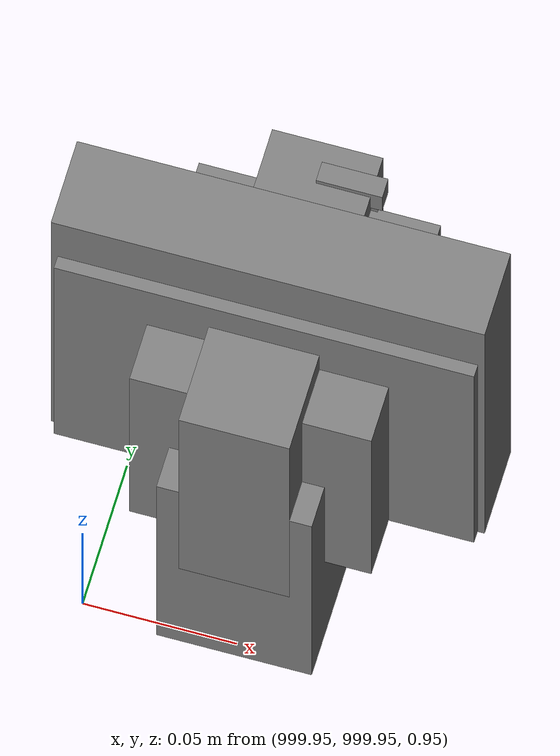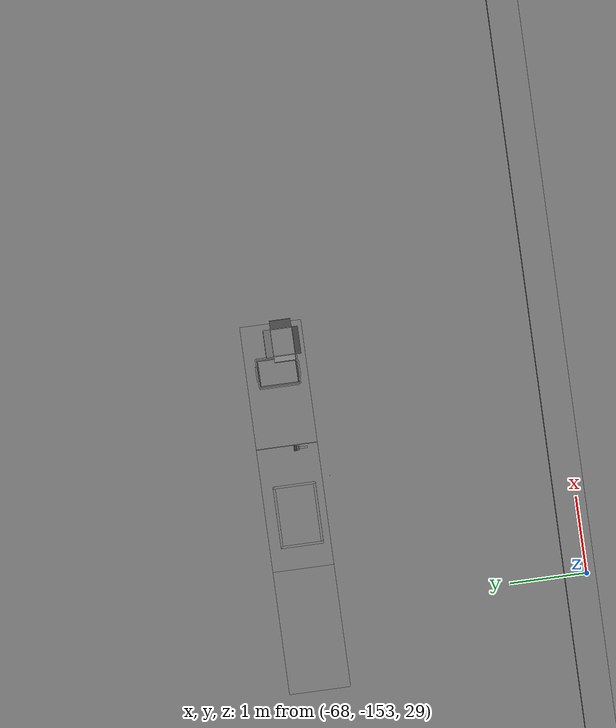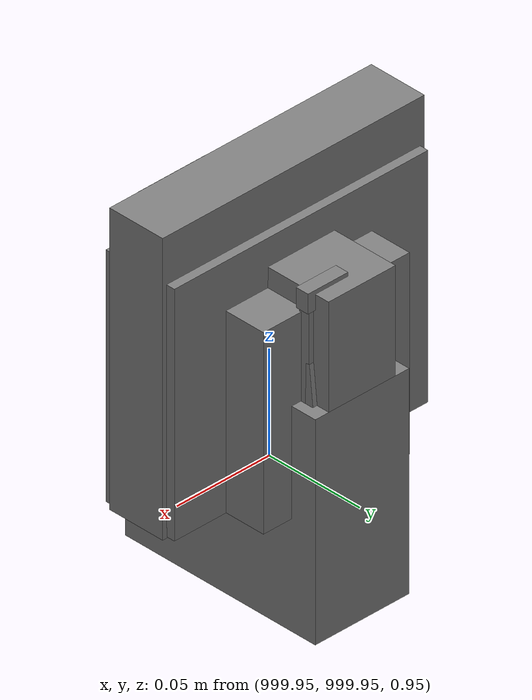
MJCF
<mujoco>
    <option gravity="0.000000000 0.000000000 -9.810000420" timestep="0.0049999999" integrator="implicitfast" density="1.225" viscosity="1.8000001e-05" noslip_iterations="10" iterations="100" sdf_iterations="50">
        <flag multiccd="disable"/>
    </option>
    <size memory="1000M"/>
    <compiler coordinate="local"/>
    <worldbody>
        <light cutoff="30" pos="0 1 1" dir="0 -1 -2"/>
        <light cutoff="30" pos="0 -1 1" dir="0 1 -2"/>
        <body pos="-64.866622925 -149.383972168 30.183746338" euler="89.999984741 89.999946594 0.000000000" name="openloong_gripper_2f85_fix_base_usda_bluebox_01">
            <geom contype="1" conaffinity="1" density="1000" type="box" material="" rgba="0.500000000 0.500000000 0.500000000 1.000000000" solimp="0.899999976 0.949999988 0.001000000" friction="1.000000000 0.005000000 0.000100000" solref="0.020000000 1.000000000" margin="0" condim="3" group="0" pos="0.276580811 0.187225342 0.000068665" quat="0.707106948 0.000077471 0.707106352 0.000077486" size="0.100000001 0.057999998 0.010000000" name="openloong_gripper_2f85_fix_base_usda_geom_CACACD40_B746_471F_BDDD_083E32125236"/>
            <geom contype="1" conaffinity="1" density="1000" type="box" material="" rgba="0.500000000 0.500000000 0.500000000 1.000000000" solimp="0.899999976 0.949999988 0.001000000" friction="1.000000000 0.005000000 0.000100000" solref="0.020000000 1.000000000" margin="0" condim="3" group="0" pos="0.000000000 0.002883911 0.000000000" quat="0.999999881 0.000000000 0.000000000 0.000000000" size="0.254000008 0.003000000 0.172000006" name="openloong_gripper_2f85_fix_base_usda_geom_1B4DEB9A_47E7_4BB0_A678_96BBA0F7B6A7"/>
            <geom contype="1" conaffinity="1" density="1000" type="box" material="" rgba="0.500000000 0.500000000 0.500000000 1.000000000" solimp="0.899999976 0.949999988 0.001000000" friction="1.000000000 0.005000000 0.000100000" solref="0.020000000 1.000000000" margin="0" condim="3" group="0" pos="0.000000000 0.124874115 0.173484802" quat="0.999796331 0.020176515 -0.000000015 0.000000030" size="0.259999990 0.119999997 0.007000000" name="openloong_gripper_2f85_fix_base_usda_geom_D1E50418_BE14_46FC_AF9C_737C2CB1189D"/>
            <geom contype="1" conaffinity="1" density="1000" type="box" material="" rgba="0.500000000 0.500000000 0.500000000 1.000000000" solimp="0.899999976 0.949999988 0.001000000" friction="1.000000000 0.005000000 0.000100000" solref="0.020000000 1.000000000" margin="0" condim="3" group="0" pos="0.000000000 0.124874115 -0.173469543" quat="0.999796331 -0.020176545 -0.000000015 0.000000000" size="0.259999990 0.119999997 0.007000000" name="openloong_gripper_2f85_fix_base_usda_geom_AD46EC87_AB56_408C_A291_FEDA4A370958"/>
            <geom contype="1" conaffinity="1" density="1000" type="box" material="" rgba="0.500000000 0.500000000 0.500000000 1.000000000" solimp="0.899999976 0.949999988 0.001000000" friction="1.000000000 0.005000000 0.000100000" solref="0.020000000 1.000000000" margin="0" condim="3" group="0" pos="0.000000000 0.214008331 0.188980103" quat="0.999912977 0.013176724 0.000000015 0.000000000" size="0.259999990 0.029999999 0.012500000" name="openloong_gripper_2f85_fix_base_usda_geom_9516C018_A6E9_4355_BDA8_E487D409759A"/>
            <geom contype="1" conaffinity="1" density="1000" type="box" material="" rgba="0.500000000 0.500000000 0.500000000 1.000000000" solimp="0.899999976 0.949999988 0.001000000" friction="1.000000000 0.005000000 0.000100000" solref="0.020000000 1.000000000" margin="0" condim="3" group="0" pos="-0.258361816 0.125289917 0.001876831" quat="0.702796936 -0.020792112 0.710783124 0.020769298" size="0.189999998 0.119999997 0.009000000" name="openloong_gripper_2f85_fix_base_usda_geom_427B5B04_E4A1_4C38_B529_15168DB82616"/>
            <geom contype="1" conaffinity="1" density="1000" type="box" material="" rgba="0.500000000 0.500000000 0.500000000 1.000000000" solimp="0.899999976 0.949999988 0.001000000" friction="1.000000000 0.005000000 0.000100000" solref="0.020000000 1.000000000" margin="0" condim="3" group="0" pos="0.000000000 0.214008331 -0.188980103" quat="0.999912977 -0.013176769 0.000000030 0.000000015" size="0.259999990 0.029999999 0.012500000" name="openloong_gripper_2f85_fix_base_usda_geom_96F92A59_515D_44DA_86FA_2047657AC8FD"/>
            <geom contype="1" conaffinity="1" density="1000" type="box" material="" rgba="0.500000000 0.500000000 0.500000000 1.000000000" solimp="0.899999976 0.949999988 0.001000000" friction="1.000000000 0.005000000 0.000100000" solref="0.020000000 1.000000000" margin="0" condim="3" group="0" pos="-0.276611328 0.187225342 0.000068665" quat="0.707106650 0.000077441 0.707106709 0.000077456" size="0.100000001 0.057999998 0.010000000" name="openloong_gripper_2f85_fix_base_usda_geom_49E50DE4_4F1F_401F_B730_B76AC81B907D"/>
            <geom contype="1" conaffinity="1" density="1000" type="box" material="" rgba="0.500000000 0.500000000 0.500000000 1.000000000" solimp="0.899999976 0.949999988 0.001000000" friction="1.000000000 0.005000000 0.000100000" solref="0.020000000 1.000000000" margin="0" condim="3" group="0" pos="0.258331299 0.125289917 0.001876831" quat="0.702851415 0.018856421 0.710823774 -0.019329369" size="0.189999998 0.119999997 0.009000000" name="openloong_gripper_2f85_fix_base_usda_geom_3B2F2DDF_A792_40DF_851C_2E0690C61ACF"/>
            <freejoint name="openloong_gripper_2f85_fix_base_usda_bluebox_01_joint"/>
            <site size="0.005000000 0.005000000 0.005000000" rgba="0.500000000 0.500000000 0.500000000 1.000000000" pos="0.000000000 0.000000000 0.000000000" quat="0.999961913 0.008726534 0.000000000 0.000000000" group="0" type="sphere" name="openloong_gripper_2f85_fix_base_usda_bluebox_01site"/>
        </body>
        <body pos="-64.496299744 -149.491867065 30.235729218" euler="0.000000000 0.000000000 89.999946594" name="openloong_gripper_2f85_fix_base_usda_cardboardbox_01">
            <geom contype="1" conaffinity="1" density="1000" type="box" material="" rgba="0.500000000 0.500000000 0.500000000 1.000000000" solimp="0.899999976 0.949999988 0.001000000" friction="1.000000000 0.005000000 0.000100000" solref="0.020000000 1.000000000" margin="0" condim="3" group="0" pos="-0.003166199 -0.004086494 0.005052090" quat="1.000000000 0.000000000 0.000000000 0.000000000" size="0.142499998 0.177500010 0.005000000" name="openloong_gripper_2f85_fix_base_usda_geom_4A3C70A4_F255_4940_BA57_8B14021E9004"/>
            <geom contype="1" conaffinity="1" density="1000" type="box" material="" rgba="0.500000000 0.500000000 0.500000000 1.000000000" solimp="0.899999976 0.949999988 0.001000000" friction="1.000000000 0.005000000 0.000100000" solref="0.020000000 1.000000000" margin="0" condim="3" group="0" pos="-0.003166199 0.170316696 0.150570869" quat="1.000000000 0.000000000 0.000000000 0.000000000" size="0.142499998 0.005000000 0.149999991" name="openloong_gripper_2f85_fix_base_usda_geom_72376515_FECA_4009_A618_F706359825D2"/>
            <geom contype="1" conaffinity="1" density="1000" type="box" material="" rgba="0.500000000 0.500000000 0.500000000 1.000000000" solimp="0.899999976 0.949999988 0.001000000" friction="1.000000000 0.005000000 0.000100000" solref="0.020000000 1.000000000" margin="0" condim="3" group="0" pos="-0.147399902 -0.005307198 0.150570869" quat="1.000000000 0.000000000 0.000000000 0.000000000" size="0.005000000 0.177500010 0.149999991" name="openloong_gripper_2f85_fix_base_usda_geom_469FDF41_E95B_4953_8F84_2B4913010A23"/>
            <geom contype="1" conaffinity="1" density="1000" type="box" material="" rgba="0.500000000 0.500000000 0.500000000 1.000000000" solimp="0.899999976 0.949999988 0.001000000" friction="1.000000000 0.005000000 0.000100000" solref="0.020000000 1.000000000" margin="0" condim="3" group="0" pos="0.140275955 -0.005307198 0.150570869" quat="1.000000000 0.000000000 0.000000000 0.000000000" size="0.005000000 0.177500010 0.149999991" name="openloong_gripper_2f85_fix_base_usda_geom_00F6F601_F7F5_4CD8_AD7F_126F36906764"/>
            <geom contype="1" conaffinity="1" density="1000" type="box" material="" rgba="0.500000000 0.500000000 0.500000000 1.000000000" solimp="0.899999976 0.949999988 0.001000000" friction="1.000000000 0.005000000 0.000100000" solref="0.020000000 1.000000000" margin="0" condim="3" group="0" pos="-0.003166199 -0.181550980 0.150570869" quat="1.000000000 0.000000000 0.000000000 0.000000000" size="0.142499998 0.005000000 0.149999991" name="openloong_gripper_2f85_fix_base_usda_geom_EAEE9AAE_65C0_44C9_82F9_09A030C518E6"/>
            <freejoint name="openloong_gripper_2f85_fix_base_usda_cardboardbox_01_joint"/>
            <site size="0.005000000 0.005000000 0.005000000" rgba="0.500000000 0.500000000 0.500000000 1.000000000" pos="0.000000000 0.000000000 0.000000000" quat="0.999961913 0.008726535 0.000000000 0.000000000" group="0" type="sphere" name="openloong_gripper_2f85_fix_base_usda_site_97F0F738_69C9_439C_A998_6C18527DB66A"/>
            <body pos="0.139160156 -0.004048347 0.301930904" euler="-179.999954224 49.383502960 179.999954224" name="openloong_gripper_2f85_fix_base_usda_A1_006">
                <geom contype="1" conaffinity="1" density="1000" type="box" material="" rgba="0.500000000 0.500000000 0.500000000 1.000000000" solimp="0.899999976 0.949999988 0.001000000" friction="1.000000000 0.005000000 0.000100000" solref="0.020000000 1.000000000" margin="0" condim="3" group="0" pos="-0.071587563 0.000009537 0.001745224" quat="0.999999881 0.000000000 0.000000000 0.000000000" size="0.071249999 0.179999992 0.002500000" name="openloong_gripper_2f85_fix_base_usda_geom_109159B6_179D_4337_A05B_448C50CE960C"/>
                <joint armature="0" stiffness="0.07" damping="0.0099999998" axis="0.000000 1.000000 0.000000" type="hinge" name="openloong_gripper_2f85_fix_base_usda_A1_006"/>
            </body>
            <body pos="-0.145902634 -0.004086494 0.301938057" euler="-180.000000000 -60.000011444 -180.000000000" name="openloong_gripper_2f85_fix_base_usda_A2_006">
                <geom contype="1" conaffinity="1" density="1000" type="box" material="" rgba="0.500000000 0.500000000 0.500000000 1.000000000" solimp="0.899999976 0.949999988 0.001000000" friction="1.000000000 0.005000000 0.000100000" solref="0.020000000 1.000000000" margin="0" condim="3" group="0" pos="0.071268082 0.000009537 0.002717972" quat="0.000002921 0.000000000 -0.000000030 0.999999881" size="0.071249999 0.179999992 0.002500000" name="openloong_gripper_2f85_fix_base_usda_geom_9AE98BE4_E0BC_4DEA_AC1B_4D4ABAEB49F2"/>
                <joint armature="0" stiffness="0.07" damping="0.0099999998" axis="0.000000 1.000000 0.000000" type="hinge" name="openloong_gripper_2f85_fix_base_usda_A2_006"/>
            </body>
            <body pos="-0.003385544 0.175991058 0.301930904" euler="-125.858116150 -0.000004561 0.000002331" name="openloong_gripper_2f85_fix_base_usda_B2_006">
                <geom contype="1" conaffinity="1" density="1000" type="box" material="" rgba="0.500000000 0.500000000 0.500000000 1.000000000" solimp="0.899999976 0.949999988 0.001000000" friction="1.000000000 0.005000000 0.000100000" solref="0.020000000 1.000000000" margin="0" condim="3" group="0" pos="0.000009537 -0.070939064 -0.002470016" quat="0.999614120 0.027776197 -0.000000015 0.000000030" size="0.137500003 0.064999998 0.005000000" name="openloong_gripper_2f85_fix_base_usda_geom_FC5955D9_3D56_4887_BC74_09C8E398B70C"/>
                <joint armature="0" stiffness="0.07" damping="0.0099999998" axis="1.000000 0.000000 0.000000" type="hinge" name="openloong_gripper_2f85_fix_base_usda_B2_006"/>
            </body>
            <body pos="-0.003385544 -0.184140205 0.301938057" euler="147.805557251 0.000000000 0.000000000" name="openloong_gripper_2f85_fix_base_usda_B1_006">
                <geom contype="1" conaffinity="1" density="1000" type="box" material="" rgba="0.500000000 0.500000000 0.500000000 1.000000000" solimp="0.899999976 0.949999988 0.001000000" friction="1.000000000 0.005000000 0.000100000" solref="0.020000000 1.000000000" margin="0" condim="3" group="0" pos="-0.000028610 0.070202351 -0.002703667" quat="0.999614179 -0.027776167 0.000000000 0.000000000" size="0.137500003 0.064999998 0.005000000" name="openloong_gripper_2f85_fix_base_usda_geom_52E6D5E5_5EFF_414B_8234_56C73EF16557"/>
                <joint armature="0" stiffness="0.07" damping="0.0099999998" axis="1.000000 0.000000 0.000000" type="hinge" name="openloong_gripper_2f85_fix_base_usda_B1_006"/>
            </body>
        </body>
        <body pos="-65.882858276 -149.481979370 30.229999542" euler="-64.487716675 0.000000000 0.000000000" name="openloong_gripper_2f85_fix_base_usda_Barcode">
            <geom contype="1" conaffinity="1" density="1000" type="box" material="" rgba="0.500000000 0.500000000 0.500000000 1.000000000" solimp="0.899999976 0.949999988 0.001000000" friction="1.000000000 0.005000000 0.000100000" solref="0.020000000 1.000000000" margin="0" condim="3" group="0" pos="0.000000000 0.013038635 0.001419067" quat="0.000000000 0.000000000 0.000000000 1.000000119" size="0.034000002 0.010000000 0.017999999" name="openloong_gripper_2f85_fix_base_usda_geom_BB5A22D9_859C_4C21_8C87_37392FFB11CA"/>
            <geom contype="1" conaffinity="1" density="1000" type="box" material="" rgba="0.500000000 0.500000000 0.500000000 1.000000000" solimp="0.899999976 0.949999988 0.001000000" friction="1.000000000 0.005000000 0.000100000" solref="0.020000000 1.000000000" margin="0" condim="3" group="0" pos="0.000000000 -0.035301208 -0.007095337" quat="0.000000000 0.000000000 -0.043619365 0.999048233" size="0.028999999 0.010000000 0.020000000" name="openloong_gripper_2f85_fix_base_usda_geom_EE611A3C_8C40_4635_A8C5_D3961B5FC894"/>
            <geom contype="1" conaffinity="1" density="1000" type="box" material="" rgba="0.500000000 0.500000000 0.500000000 1.000000000" solimp="0.899999976 0.949999988 0.001000000" friction="1.000000000 0.005000000 0.000100000" solref="0.020000000 1.000000000" margin="0" condim="3" group="0" pos="0.000000000 -0.043411255 -0.011749268" quat="0.922262907 0.386563420 0.000000000 0.000000000" size="0.026000001 0.010000000 0.020000000" name="openloong_gripper_2f85_fix_base_usda_geom_C0977EE0_DD18_4DA6_82B8_48EB0E73B7B8"/>
            <geom contype="1" conaffinity="1" density="1000" type="box" material="" rgba="0.500000000 0.500000000 0.500000000 1.000000000" solimp="0.899999976 0.949999988 0.001000000" friction="1.000000000 0.005000000 0.000100000" solref="0.020000000 1.000000000" margin="0" condim="3" group="0" pos="0.000000000 -0.016967773 -0.031860352" quat="0.000000000 0.000000000 0.000000000 1.000000119" size="0.008000000 0.010000000 0.013000000" name="openloong_gripper_2f85_fix_base_usda_geom_985F921C_B7FC_4169_B6AF_74DE86FDB3EA"/>
            <geom contype="1" conaffinity="1" density="1000" type="box" material="" rgba="0.500000000 0.500000000 0.500000000 1.000000000" solimp="0.899999976 0.949999988 0.001000000" friction="1.000000000 0.005000000 0.000100000" solref="0.020000000 1.000000000" margin="0" condim="3" group="0" pos="0.000000000 -0.001869202 0.000312805" quat="0.953716993 0.300705761 0.000000000 0.000000000" size="0.032000002 0.010000000 0.018999999" name="openloong_gripper_2f85_fix_base_usda_geom_5116DC4F_BE8B_4992_9F65_9A7E918D243D"/>
            <geom contype="1" conaffinity="1" density="1000" type="box" material="" rgba="0.500000000 0.500000000 0.500000000 1.000000000" solimp="0.899999976 0.949999988 0.001000000" friction="1.000000000 0.005000000 0.000100000" solref="0.020000000 1.000000000" margin="0" condim="3" group="0" pos="0.000000000 -0.019531250 -0.003173828" quat="0.953716993 0.300705761 0.000000000 0.000000000" size="0.030999999 0.010000000 0.020000000" name="openloong_gripper_2f85_fix_base_usda_geom_B11B4675_D80A_4B21_A174_0B9C7DFA7592"/>
            <geom contype="1" conaffinity="1" density="1000" type="box" material="" rgba="0.500000000 0.500000000 0.500000000 1.000000000" solimp="0.899999976 0.949999988 0.001000000" friction="1.000000000 0.005000000 0.000100000" solref="0.020000000 1.000000000" margin="0" condim="3" group="0" pos="0.000000000 -0.035301208 -0.007095337" quat="0.953716993 0.300705761 0.000000000 0.000000000" size="0.028999999 0.010000000 0.020000000" name="openloong_gripper_2f85_fix_base_usda_geom_6F220CAD_645F_43D6_BCD6_B30FB8C46EBF"/>
            <geom contype="1" conaffinity="1" density="1000" type="box" material="" rgba="0.500000000 0.500000000 0.500000000 1.000000000" solimp="0.899999976 0.949999988 0.001000000" friction="1.000000000 0.005000000 0.000100000" solref="0.020000000 1.000000000" margin="0" condim="3" group="0" pos="0.000000000 -0.042617798 -0.071121216" quat="0.000000000 0.000000000 0.000000000 1.000000119" size="0.013000000 0.021000000 0.059999999" name="openloong_gripper_2f85_fix_base_usda_geom_3AFB8F48_8B58_4D52_9E93_62620CDA0746"/>
            <freejoint name="openloong_gripper_2f85_fix_base_usda_Barcode_joint"/>
            <site size="0.005000000 0.005000000 0.005000000" rgba="0.500000000 0.500000000 0.500000000 1.000000000" pos="0.000000000 0.000000000 0.000000000" quat="1.000000000 0.000000000 0.000000000 0.000000000" group="0" type="sphere" name="openloong_gripper_2f85_fix_base_usda_Barcode_site"/>
        </body>
        <body pos="-66.745018005 -149.392349243 30.184000015" euler="0.000000000 0.000000000 89.999946594" name="[22333763581784]_Basket_01">
            <geom contype="1" conaffinity="1" density="1000" type="box" material="" rgba="0.500000000 0.500000000 0.500000000 1.000000000" solimp="0.899999976 0.949999988 0.001000000" friction="1.000000000 0.005000000 0.000100000" solref="0.020000000 1.000000000" margin="0" condim="3" group="0" pos="-0.052425385 0.389207840 0.089787483" quat="0.707107008 0.000000000 0.000000000 0.707106411" size="0.014249999 0.014249999 0.059999999" name="[22333763581784]_geom_A78294E4_0EEB_4B37_868E_BB4B3A3C6429"/>
            <geom contype="1" conaffinity="1" density="1000" type="box" material="" rgba="0.500000000 0.500000000 0.500000000 1.000000000" solimp="0.899999976 0.949999988 0.001000000" friction="1.000000000 0.005000000 0.000100000" solref="0.020000000 1.000000000" margin="0" condim="3" group="0" pos="0.264015198 -0.133043289 0.089787483" quat="0.707107008 0.000000000 0.000000000 0.707106411" size="0.014249999 0.014249999 0.059999999" name="[22333763581784]_geom_9E4E2B14_78AC_4E59_A0C8_D6B716A1EA77"/>
            <geom contype="1" conaffinity="1" density="1000" type="box" material="" rgba="0.500000000 0.500000000 0.500000000 1.000000000" solimp="0.899999976 0.949999988 0.001000000" friction="1.000000000 0.005000000 0.000100000" solref="0.020000000 1.000000000" margin="0" condim="3" group="0" pos="-0.264015198 -0.265548706 0.089793205" quat="0.707107008 0.000000000 0.000000000 0.707106411" size="0.014249999 0.014249999 0.059999999" name="[22333763581784]_geom_1B1E97A1_5A66_4EAF_B2F4_C929AEF41672"/>
            <geom contype="1" conaffinity="1" density="1000" type="box" material="" rgba="0.500000000 0.500000000 0.500000000 1.000000000" solimp="0.899999976 0.949999988 0.001000000" friction="1.000000000 0.005000000 0.000100000" solref="0.020000000 1.000000000" margin="0" condim="3" group="0" pos="-0.160263062 -0.389322281 0.089793205" quat="0.707107008 0.000000000 0.000000000 0.707106411" size="0.014249999 0.014249999 0.059999999" name="[22333763581784]_geom_8F6E9F72_99F2_4AD4_AC36_DBAF58B2CD10"/>
            <geom contype="1" conaffinity="1" density="1000" type="box" material="" rgba="0.500000000 0.500000000 0.500000000 1.000000000" solimp="0.899999976 0.949999988 0.001000000" friction="1.000000000 0.005000000 0.000100000" solref="0.020000000 1.000000000" margin="0" condim="3" group="0" pos="0.162265778 -0.389322281 0.089787483" quat="0.707107008 0.000000000 0.000000000 0.707106411" size="0.014249999 0.014249999 0.059999999" name="[22333763581784]_geom_8B2DBB36_7EA8_4AD2_9E76_245D8B14AE9B"/>
            <geom contype="1" conaffinity="1" density="1000" type="box" material="" rgba="0.500000000 0.500000000 0.500000000 1.000000000" solimp="0.899999976 0.949999988 0.001000000" friction="1.000000000 0.005000000 0.000100000" solref="0.020000000 1.000000000" margin="0" condim="3" group="0" pos="0.264015198 0.389207840 0.089787483" quat="0.707107008 0.000000000 0.000000000 0.707106411" size="0.014249999 0.014249999 0.059999999" name="[22333763581784]_geom_83E325A8_2EFB_438E_9C93_7745474BB237"/>
            <geom contype="1" conaffinity="1" density="1000" type="box" material="" rgba="0.500000000 0.500000000 0.500000000 1.000000000" solimp="0.899999976 0.949999988 0.001000000" friction="1.000000000 0.005000000 0.000100000" solref="0.020000000 1.000000000" margin="0" condim="3" group="0" pos="-0.264015198 -0.133043289 0.089793205" quat="0.707107008 0.000000000 0.000000000 0.707106411" size="0.014249999 0.014249999 0.059999999" name="[22333763581784]_geom_2F9492B5_CDA5_47D0_B4E6_5A04082728A0"/>
            <geom contype="1" conaffinity="1" density="1000" type="box" material="" rgba="0.500000000 0.500000000 0.500000000 1.000000000" solimp="0.899999976 0.949999988 0.001000000" friction="1.000000000 0.005000000 0.000100000" solref="0.020000000 1.000000000" margin="0" condim="3" group="0" pos="-0.264026642 0.269256592 0.089793205" quat="0.707107008 0.000000000 0.000000000 0.707106411" size="0.014249999 0.014249999 0.059999999" name="[22333763581784]_geom_889DEDB5_CCE2_4C92_982C_5FC853470D1F"/>
            <geom contype="1" conaffinity="1" density="1000" type="box" material="" rgba="0.500000000 0.500000000 0.500000000 1.000000000" solimp="0.899999976 0.949999988 0.001000000" friction="1.000000000 0.005000000 0.000100000" solref="0.020000000 1.000000000" margin="0" condim="3" group="0" pos="0.054462433 0.389207840 0.089787483" quat="0.707107008 0.000000000 0.000000000 0.707106411" size="0.014249999 0.014249999 0.059999999" name="[22333763581784]_geom_A2B3FD43_691B_418C_8810_5196542CFDA8"/>
            <geom contype="1" conaffinity="1" density="1000" type="box" material="" rgba="0.500000000 0.500000000 0.500000000 1.000000000" solimp="0.899999976 0.949999988 0.001000000" friction="1.000000000 0.005000000 0.000100000" solref="0.020000000 1.000000000" margin="0" condim="3" group="0" pos="0.054462433 -0.389322281 0.089787483" quat="0.707107008 0.000000000 0.000000000 0.707106411" size="0.014249999 0.014249999 0.059999999" name="[22333763581784]_geom_67D84651_1126_4FBB_88F9_1636EEA742D9"/>
            <geom contype="1" conaffinity="1" density="1000" type="box" material="" rgba="0.500000000 0.500000000 0.500000000 1.000000000" solimp="0.899999976 0.949999988 0.001000000" friction="1.000000000 0.005000000 0.000100000" solref="0.020000000 1.000000000" margin="0" condim="3" group="0" pos="0.264015198 0.269256592 0.089793205" quat="0.707107008 0.000000000 0.000000000 0.707106411" size="0.014249999 0.014249999 0.059999999" name="[22333763581784]_geom_0DE437B4_14EB_416F_9069_2D45C2A9E771"/>
            <geom contype="1" conaffinity="1" density="1000" type="box" material="" rgba="0.500000000 0.500000000 0.500000000 1.000000000" solimp="0.899999976 0.949999988 0.001000000" friction="1.000000000 0.005000000 0.000100000" solref="0.020000000 1.000000000" margin="0" condim="3" group="0" pos="0.264015198 -0.389322281 0.089787483" quat="0.707107008 0.000000000 0.000000000 0.707106411" size="0.014249999 0.014249999 0.059999999" name="[22333763581784]_geom_CA0EA7E6_9044_4BC5_BCF4_4D1D5F304463"/>
            <geom contype="1" conaffinity="1" density="1000" type="box" material="" rgba="0.500000000 0.500000000 0.500000000 1.000000000" solimp="0.899999976 0.949999988 0.001000000" friction="1.000000000 0.005000000 0.000100000" solref="0.020000000 1.000000000" margin="0" condim="3" group="0" pos="0.000000000 0.000000000 0.015998840" quat="0.707107008 0.000000000 0.000000000 0.707106411" size="0.403499991 0.279000014 0.015750000" name="[22333763581784]_geom_5376931B_00E7_4873_A56C_CBDACB7BFD33"/>
            <geom contype="1" conaffinity="1" density="1000" type="box" material="" rgba="0.500000000 0.500000000 0.500000000 1.000000000" solimp="0.899999976 0.949999988 0.001000000" friction="1.000000000 0.005000000 0.000100000" solref="0.020000000 1.000000000" margin="0" condim="3" group="0" pos="0.000000000 -0.389476776 0.163619041" quat="0.707107008 0.000000000 0.000000000 0.707106411" size="0.015000000 0.277500004 0.015750000" name="[22333763581784]_geom_0B8B03C1_12CE_47C7_9CA6_73CA6EF1CEED"/>
            <geom contype="1" conaffinity="1" density="1000" type="box" material="" rgba="0.500000000 0.500000000 0.500000000 1.000000000" solimp="0.899999976 0.949999988 0.001000000" friction="1.000000000 0.005000000 0.000100000" solref="0.020000000 1.000000000" margin="0" condim="3" group="0" pos="0.162265778 0.389207840 0.089787483" quat="0.707107008 0.000000000 0.000000000 0.707106411" size="0.014249999 0.014249999 0.059999999" name="[22333763581784]_geom_AD9022D3_6269_44F8_BC93_67D6415D1A0F"/>
            <geom contype="1" conaffinity="1" density="1000" type="box" material="" rgba="0.500000000 0.500000000 0.500000000 1.000000000" solimp="0.899999976 0.949999988 0.001000000" friction="1.000000000 0.005000000 0.000100000" solref="0.020000000 1.000000000" margin="0" condim="3" group="0" pos="0.000000000 0.389471054 0.163619041" quat="0.707107008 0.000000000 0.000000000 0.707106411" size="0.015000000 0.277500004 0.015750000" name="[22333763581784]_geom_4DF51A24_3252_41FD_95B2_D99D7514966A"/>
            <geom contype="1" conaffinity="1" density="1000" type="box" material="" rgba="0.500000000 0.500000000 0.500000000 1.000000000" solimp="0.899999976 0.949999988 0.001000000" friction="1.000000000 0.005000000 0.000100000" solref="0.020000000 1.000000000" margin="0" condim="3" group="0" pos="-0.263511658 0.000000000 0.163619041" quat="0.707107008 0.000000000 0.000000000 0.707106411" size="0.403499991 0.015000000 0.015750000" name="[22333763581784]_geom_1311684B_669E_4890_AC93_49B55BFD906F"/>
            <geom contype="1" conaffinity="1" density="1000" type="box" material="" rgba="0.500000000 0.500000000 0.500000000 1.000000000" solimp="0.899999976 0.949999988 0.001000000" friction="1.000000000 0.005000000 0.000100000" solref="0.020000000 1.000000000" margin="0" condim="3" group="0" pos="-0.264015198 0.141334534 0.089793205" quat="0.707107008 0.000000000 0.000000000 0.707106411" size="0.014249999 0.014249999 0.059999999" name="[22333763581784]_geom_24283197_6E7F_4671_B917_CE7C9F60EDCC"/>
            <geom contype="1" conaffinity="1" density="1000" type="box" material="" rgba="0.500000000 0.500000000 0.500000000 1.000000000" solimp="0.899999976 0.949999988 0.001000000" friction="1.000000000 0.005000000 0.000100000" solref="0.020000000 1.000000000" margin="0" condim="3" group="0" pos="0.264015198 -0.265548706 0.089787483" quat="0.707107008 0.000000000 0.000000000 0.707106411" size="0.014249999 0.014249999 0.059999999" name="[22333763581784]_geom_AFBA0762_F553_455E_AB19_2E5B366E2AA4"/>
            <geom contype="1" conaffinity="1" density="1000" type="box" material="" rgba="0.500000000 0.500000000 0.500000000 1.000000000" solimp="0.899999976 0.949999988 0.001000000" friction="1.000000000 0.005000000 0.000100000" solref="0.020000000 1.000000000" margin="0" condim="3" group="0" pos="-0.160263062 0.389207840 0.089787483" quat="0.707107008 0.000000000 0.000000000 0.707106411" size="0.014249999 0.014249999 0.059999999" name="[22333763581784]_geom_FF677E06_34FC_4CC7_9989_10E5FF81AE4E"/>
            <geom contype="1" conaffinity="1" density="1000" type="box" material="" rgba="0.500000000 0.500000000 0.500000000 1.000000000" solimp="0.899999976 0.949999988 0.001000000" friction="1.000000000 0.005000000 0.000100000" solref="0.020000000 1.000000000" margin="0" condim="3" group="0" pos="-0.052425385 -0.389322281 0.089787483" quat="0.707107008 0.000000000 0.000000000 0.707106411" size="0.014249999 0.014249999 0.059999999" name="[22333763581784]_geom_2E6A1A47_FC5B_4AE7_B837_2C75C9D3AC7D"/>
            <geom contype="1" conaffinity="1" density="1000" type="box" material="" rgba="0.500000000 0.500000000 0.500000000 1.000000000" solimp="0.899999976 0.949999988 0.001000000" friction="1.000000000 0.005000000 0.000100000" solref="0.020000000 1.000000000" margin="0" condim="3" group="0" pos="-0.264026642 -0.389322281 0.089793205" quat="0.707107008 0.000000000 0.000000000 0.707106411" size="0.014249999 0.014249999 0.059999999" name="[22333763581784]_geom_E3BFEFDC_915B_432B_96B3_A6A342D789DA"/>
            <geom contype="1" conaffinity="1" density="1000" type="box" material="" rgba="0.500000000 0.500000000 0.500000000 1.000000000" solimp="0.899999976 0.949999988 0.001000000" friction="1.000000000 0.005000000 0.000100000" solref="0.020000000 1.000000000" margin="0" condim="3" group="0" pos="0.264015198 0.141334534 0.089787483" quat="0.707107008 0.000000000 0.000000000 0.707106411" size="0.014249999 0.014249999 0.059999999" name="[22333763581784]_geom_2AE9E33F_3DDB_4712_99BD_04622B856DCB"/>
            <geom contype="1" conaffinity="1" density="1000" type="box" material="" rgba="0.500000000 0.500000000 0.500000000 1.000000000" solimp="0.899999976 0.949999988 0.001000000" friction="1.000000000 0.005000000 0.000100000" solref="0.020000000 1.000000000" margin="0" condim="3" group="0" pos="-0.264015198 0.389207840 0.089793205" quat="0.707107008 0.000000000 0.000000000 0.707106411" size="0.014249999 0.014249999 0.059999999" name="[22333763581784]_geom_85FE2051_1EBD_40A5_8FD8_FEE379A79289"/>
            <geom contype="1" conaffinity="1" density="1000" type="box" material="" rgba="0.500000000 0.500000000 0.500000000 1.000000000" solimp="0.899999976 0.949999988 0.001000000" friction="1.000000000 0.005000000 0.000100000" solref="0.020000000 1.000000000" margin="0" condim="3" group="0" pos="0.264015198 0.004480362 0.089787483" quat="0.707107008 0.000000000 0.000000000 0.707106411" size="0.014249999 0.014249999 0.059999999" name="[22333763581784]_geom_DE2C74CB_154E_4DED_BC9A_2B4555CBD00C"/>
            <geom contype="1" conaffinity="1" density="1000" type="box" material="" rgba="0.500000000 0.500000000 0.500000000 1.000000000" solimp="0.899999976 0.949999988 0.001000000" friction="1.000000000 0.005000000 0.000100000" solref="0.020000000 1.000000000" margin="0" condim="3" group="0" pos="0.263694763 -0.000011444 0.163619041" quat="0.707107008 0.000000000 0.000000000 0.707106411" size="0.403499991 0.015000000 0.015750000" name="[22333763581784]_geom_294304A4_32A2_480C_9BA4_12615E9B1B45"/>
            <geom contype="1" conaffinity="1" density="1000" type="box" material="" rgba="0.500000000 0.500000000 0.500000000 1.000000000" solimp="0.899999976 0.949999988 0.001000000" friction="1.000000000 0.005000000 0.000100000" solref="0.020000000 1.000000000" margin="0" condim="3" group="0" pos="-0.264015198 0.004480362 0.089793205" quat="0.707107008 0.000000000 0.000000000 0.707106411" size="0.014249999 0.014249999 0.059999999" name="[22333763581784]_geom_AEFC8CAC_D19A_4CD4_B16D_F33534D2A69C"/>
            <freejoint name="[22333763581784]_joint_B36BF51B_9FA9_4A0A_B321_B899B736D629"/>
        </body>
        <body pos="0.000000000 0.000000000 0.000000000" euler="0.000000000 0.000000000 0.000000000" name="Static Objects_Static Objects">
            <geom contype="1" conaffinity="1" density="1000" type="box" material="" rgba="0.500000000 0.500000000 0.500000000 1.000000000" solimp="0.899999976 0.949999988 0.001000000" friction="1.000000000 0.005000000 0.000100000" solref="0.020000000 1.000000000" margin="0" condim="3" group="0" pos="-67.544113159 -149.365814209 29.727830887" quat="0.500000417 0.499999970 0.499999553 0.499999970" size="0.381000012 0.319999993 0.041000001" name="Static Objects_geom_C79817F3_3F75_439A_9582_D51D30D77F71"/>
            <geom contype="1" conaffinity="1" density="1000" type="box" material="" rgba="0.500000000 0.500000000 0.500000000 1.000000000" solimp="0.899999976 0.949999988 0.001000000" friction="1.000000000 0.005000000 0.000100000" solref="0.020000000 1.000000000" margin="0" condim="3" group="0" pos="-68.239501953 -149.365814209 30.086868286" quat="0.500000417 0.499999970 0.499999553 0.499999970" size="0.370999992 0.039500002 0.745000005" name="Static Objects_geom_46C7B1F4_833D_4C6D_8B7C_69925925FB29"/>
            <geom contype="1" conaffinity="1" density="1000" type="box" material="" rgba="0.500000000 0.500000000 0.500000000 1.000000000" solimp="0.899999976 0.949999988 0.001000000" friction="1.000000000 0.005000000 0.000100000" solref="0.020000000 1.000000000" margin="0" condim="3" group="0" pos="-68.239501953 -149.365814209 30.147235870" quat="0.500000417 0.499999970 0.499999553 0.499999970" size="0.400000006 0.022000000 0.800000012" name="Static Objects_geom_BE515B71_C27A_4216_A64F_9E78F476968E"/>
            <geom contype="1" conaffinity="1" density="1000" type="box" material="" rgba="0.500000000 0.500000000 0.500000000 1.000000000" solimp="0.899999976 0.949999988 0.001000000" friction="1.000000000 0.005000000 0.000100000" solref="0.020000000 1.000000000" margin="0" condim="3" group="0" pos="-68.934890747 -149.365814209 29.727830887" quat="0.500000417 0.499999970 0.499999553 0.499999970" size="0.381000012 0.319999993 0.041000001" name="Static Objects_geom_8DE6FF52_ECF9_4850_82C9_70203BE79C20"/>
            <geom contype="1" conaffinity="1" density="1000" type="box" material="" rgba="0.500000000 0.500000000 0.500000000 1.000000000" solimp="0.899999976 0.949999988 0.001000000" friction="1.000000000 0.005000000 0.000100000" solref="0.020000000 1.000000000" margin="0" condim="3" group="0" pos="-68.239501953 -149.365814209 29.561563492" quat="0.500000417 0.499999970 0.499999553 0.499999970" size="0.020000000 0.022000000 0.660000026" name="Static Objects_geom_BA666752_14A0_4CBA_B2B5_6B7C77425530"/>
            <geom contype="1" conaffinity="1" density="1000" type="box" material="" rgba="0.500000000 0.500000000 0.500000000 1.000000000" solimp="0.899999976 0.949999988 0.001000000" friction="1.000000000 0.005000000 0.000100000" solref="0.020000000 1.000000000" margin="0" condim="3" group="0" pos="-65.945671082 -149.365814209 29.727830887" quat="0.500000417 0.499999970 0.499999553 0.499999970" size="0.381000012 0.319999993 0.041000001" name="Static Objects_geom_B8084C3A_4BB0_4AB7_B0B6_E7DDCFAC4EDD"/>
            <geom contype="1" conaffinity="1" density="1000" type="box" material="" rgba="0.500000000 0.500000000 0.500000000 1.000000000" solimp="0.899999976 0.949999988 0.001000000" friction="1.000000000 0.005000000 0.000100000" solref="0.020000000 1.000000000" margin="0" condim="3" group="0" pos="-66.641059875 -149.365814209 30.086868286" quat="0.500000417 0.499999970 0.499999553 0.499999970" size="0.370999992 0.039500002 0.745000005" name="Static Objects_geom_BE281623_7097_4B10_BA95_CE8D0BE538BE"/>
            <geom contype="1" conaffinity="1" density="1000" type="box" material="" rgba="0.500000000 0.500000000 0.500000000 1.000000000" solimp="0.899999976 0.949999988 0.001000000" friction="1.000000000 0.005000000 0.000100000" solref="0.020000000 1.000000000" margin="0" condim="3" group="0" pos="-66.641059875 -149.365814209 30.147235870" quat="0.500000417 0.499999970 0.499999553 0.499999970" size="0.400000006 0.022000000 0.800000012" name="Static Objects_geom_33B19DD0_E9EA_43D9_9ACE_5762B6AD3DFF"/>
            <geom contype="1" conaffinity="1" density="1000" type="box" material="" rgba="0.500000000 0.500000000 0.500000000 1.000000000" solimp="0.899999976 0.949999988 0.001000000" friction="1.000000000 0.005000000 0.000100000" solref="0.020000000 1.000000000" margin="0" condim="3" group="0" pos="-67.336448669 -149.365814209 29.727830887" quat="0.500000417 0.499999970 0.499999553 0.499999970" size="0.381000012 0.319999993 0.041000001" name="Static Objects_geom_61055450_4512_4F45_967B_1111DB3060BE"/>
            <geom contype="1" conaffinity="1" density="1000" type="box" material="" rgba="0.500000000 0.500000000 0.500000000 1.000000000" solimp="0.899999976 0.949999988 0.001000000" friction="1.000000000 0.005000000 0.000100000" solref="0.020000000 1.000000000" margin="0" condim="3" group="0" pos="-66.641059875 -149.365814209 29.561563492" quat="0.500000417 0.499999970 0.499999553 0.499999970" size="0.020000000 0.022000000 0.660000026" name="Static Objects_geom_5C0FFECB_B66C_4570_A174_E053DED7177A"/>
            <geom contype="1" conaffinity="1" density="1000" type="box" material="" rgba="0.500000000 0.500000000 0.500000000 1.000000000" solimp="0.899999976 0.949999988 0.001000000" friction="1.000000000 0.005000000 0.000100000" solref="0.020000000 1.000000000" margin="0" condim="3" group="0" pos="-64.338577271 -149.365814209 29.727830887" quat="0.500000417 0.499999970 0.499999553 0.499999970" size="0.381000012 0.319999993 0.041000001" name="Static Objects_geom_F157764E_70C9_4320_8931_3C12CC549D05"/>
            <geom contype="1" conaffinity="1" density="1000" type="box" material="" rgba="0.500000000 0.500000000 0.500000000 1.000000000" solimp="0.899999976 0.949999988 0.001000000" friction="1.000000000 0.005000000 0.000100000" solref="0.020000000 1.000000000" margin="0" condim="3" group="0" pos="-65.033966064 -149.365814209 30.086868286" quat="0.500000417 0.499999970 0.499999553 0.499999970" size="0.370999992 0.039500002 0.745000005" name="Static Objects_geom_0347D417_FA02_4A49_804B_286F78EC200F"/>
            <geom contype="1" conaffinity="1" density="1000" type="box" material="" rgba="0.500000000 0.500000000 0.500000000 1.000000000" solimp="0.899999976 0.949999988 0.001000000" friction="1.000000000 0.005000000 0.000100000" solref="0.020000000 1.000000000" margin="0" condim="3" group="0" pos="-65.033966064 -149.365814209 30.147235870" quat="0.500000417 0.499999970 0.499999553 0.499999970" size="0.400000006 0.022000000 0.800000012" name="Static Objects_geom_104FF54C_BC38_4BBE_B7B0_1DE886E5EA3D"/>
            <geom contype="1" conaffinity="1" density="1000" type="box" material="" rgba="0.500000000 0.500000000 0.500000000 1.000000000" solimp="0.899999976 0.949999988 0.001000000" friction="1.000000000 0.005000000 0.000100000" solref="0.020000000 1.000000000" margin="0" condim="3" group="0" pos="-65.729354858 -149.365814209 29.727830887" quat="0.500000417 0.499999970 0.499999553 0.499999970" size="0.381000012 0.319999993 0.041000001" name="Static Objects_geom_292397BA_85CF_4B4E_9D2C_AD7B3B8E6F3C"/>
            <geom contype="1" conaffinity="1" density="1000" type="box" material="" rgba="0.500000000 0.500000000 0.500000000 1.000000000" solimp="0.899999976 0.949999988 0.001000000" friction="1.000000000 0.005000000 0.000100000" solref="0.020000000 1.000000000" margin="0" condim="3" group="0" pos="-65.033966064 -149.365814209 29.561563492" quat="0.500000417 0.499999970 0.499999553 0.499999970" size="0.020000000 0.022000000 0.660000026" name="Static Objects_geom_127223F6_2BC3_4426_9801_F36B46CA73BD"/>
            <geom contype="1" conaffinity="1" density="1000" type="box" material="" rgba="0.500000000 0.500000000 0.500000000 1.000000000" solimp="0.899999976 0.949999988 0.001000000" friction="1.000000000 0.005000000 0.000100000" solref="0.020000000 1.000000000" margin="0" condim="3" group="0" pos="-61.754566193 -137.853729248 33.906845093" quat="0.707107067 0.000000000 0.000000000 0.707106471" size="0.759999990 0.759999990 4.500000000" name="Static Objects_geom_2EC1B4A3_B421_453C_A1AD_24C37D5831F3"/>
            <geom contype="1" conaffinity="1" density="1000" type="box" material="" rgba="0.500000000 0.500000000 0.500000000 1.000000000" solimp="0.899999976 0.949999988 0.001000000" friction="1.000000000 0.005000000 0.000100000" solref="0.020000000 1.000000000" margin="0" condim="3" group="0" pos="-57.511135101 -144.927108765 31.707921982" quat="1.000000000 0.000000000 0.000000000 0.000000000" size="0.200000003 8.000000000 2.299999952" name="Static Objects_geom_EC43CA55_5DD9_4FFA_B3B9_8DC0160E4278"/>
            <geom contype="1" conaffinity="1" density="1000" type="box" material="" rgba="0.500000000 0.500000000 0.500000000 1.000000000" solimp="0.899999976 0.949999988 0.001000000" friction="1.000000000 0.005000000 0.000100000" solref="0.020000000 1.000000000" margin="0" condim="3" group="0" pos="-80.517646790 -157.574050903 31.688196182" quat="0.707107067 0.000000000 0.000000000 0.707106471" size="0.600000024 0.600000024 2.299999952" name="Static Objects_geom_1C5526B8_6D54_4618_A7F5_3A5BBE47917C"/>
            <geom contype="1" conaffinity="1" density="1000" type="box" material="" rgba="0.500000000 0.500000000 0.500000000 1.000000000" solimp="0.899999976 0.949999988 0.001000000" friction="1.000000000 0.005000000 0.000100000" solref="0.020000000 1.000000000" margin="0" condim="3" group="0" pos="-80.711044312 -147.414932251 31.666158676" quat="1.000000000 0.000000000 0.000000000 0.000000000" size="0.200000003 10.000000000 2.299999952" name="Static Objects_geom_C559D637_2141_433C_A8A9_00E06EF08C91"/>
            <geom contype="1" conaffinity="1" density="1000" type="box" material="" rgba="0.500000000 0.500000000 0.500000000 1.000000000" solimp="0.899999976 0.949999988 0.001000000" friction="1.000000000 0.005000000 0.000100000" solref="0.020000000 1.000000000" margin="0" condim="3" group="0" pos="-57.687217712 -137.434692383 31.688196182" quat="0.707107067 0.000000000 0.000000000 0.707106471" size="0.600000024 0.600000024 2.299999952" name="Static Objects_geom_C298F86D_917F_4C6C_BA37_CC7FDDF55E6E"/>
            <geom contype="1" conaffinity="1" density="1000" type="box" material="" rgba="0.500000000 0.500000000 0.500000000 1.000000000" solimp="0.899999976 0.949999988 0.001000000" friction="1.000000000 0.005000000 0.000100000" solref="0.020000000 1.000000000" margin="0" condim="3" group="0" pos="-69.537033081 -140.263229370 31.714921951" quat="0.707107067 0.000000000 0.000000000 0.707106471" size="0.759999990 4.500000000 2.299999952" name="Static Objects_geom_BDB87B64_502B_4B98_94E8_078B0FE60EB0"/>
            <geom contype="1" conaffinity="1" density="1000" type="box" material="" rgba="0.500000000 0.500000000 0.500000000 1.000000000" solimp="0.899999976 0.949999988 0.001000000" friction="1.000000000 0.005000000 0.000100000" solref="0.020000000 1.000000000" margin="0" condim="3" group="0" pos="-80.073638916 -137.853713989 33.906845093" quat="0.707107067 0.000000000 0.000000000 0.707106471" size="0.759999990 0.759999990 4.500000000" name="Static Objects_geom_033F0500_9240_44C8_8099_4BCF482AC259"/>
            <geom contype="1" conaffinity="1" density="1000" type="box" material="" rgba="0.500000000 0.500000000 0.500000000 1.000000000" solimp="0.899999976 0.949999988 0.001000000" friction="1.000000000 0.005000000 0.000100000" solref="0.020000000 1.000000000" margin="0" condim="3" group="0" pos="-73.406707764 -155.734664917 31.707921982" quat="1.000000000 0.000000000 0.000000000 0.000000000" size="0.200000003 3.000000000 2.299999952" name="Static Objects_geom_C1180196_9CD7_42E3_8DD6_D8DCF881CFD6"/>
            <geom contype="1" conaffinity="1" density="1000" type="box" material="" rgba="0.500000000 0.500000000 0.500000000 1.000000000" solimp="0.899999976 0.949999988 0.001000000" friction="1.000000000 0.005000000 0.000100000" solref="0.020000000 1.000000000" margin="0" condim="3" group="0" pos="-68.497543335 -137.448257446 31.707921982" quat="0.707107067 0.000000000 0.000000000 0.707106471" size="0.200000003 14.000000000 2.299999952" name="Static Objects_geom_33E9E1FB_F442_46D5_94AC_DDDE0919DA98"/>
            <geom contype="1" conaffinity="1" density="1000" type="cylinder" material="" rgba="0.500000000 0.500000000 0.500000000 1.000000000" solimp="0.899999976 0.949999988 0.001000000" friction="1.000000000 0.005000000 0.000100000" solref="0.020000000 1.000000000" margin="0" condim="3" group="0" pos="-68.868522644 -142.134506226 31.711090088" quat="0.707107067 0.000000000 0.000000000 0.707106471" size="0.509999990 2.299999952 1.000000000" name="Static Objects_geom_169EC219_B66B_458B_9FFD_C93EC32C162A"/>
            <geom contype="1" conaffinity="1" density="1000" type="plane" material="" rgba="0.500000000 0.500000000 0.500000000 1.000000000" solimp="0.899999976 0.949999988 0.001000000" friction="1.000000000 0.005000000 0.000100000" solref="0.020000000 1.000000000" margin="0" condim="3" group="0" pos="-72.873703003 -147.131927490 29.409669876" quat="1.000000000 0.000000000 0.000000000 0.000000000" size="18.000000000 14.000000000 1.000000000" name="Static Objects_geom_62F40829_F35B_4E35_B576_81E77622FCA4"/>
            <geom contype="1" conaffinity="1" density="1000" type="box" material="" rgba="0.500000000 0.500000000 0.500000000 1.000000000" solimp="0.899999976 0.949999988 0.001000000" friction="1.000000000 0.005000000 0.000100000" solref="0.020000000 1.000000000" margin="0" condim="3" group="0" pos="-79.943580627 -157.782272339 31.707921982" quat="0.707107067 0.000000000 0.000000000 0.707106471" size="0.200000003 7.000000000 2.299999952" name="Static Objects_geom_12ED060F_A246_427B_84AE_213374A04CEF"/>
            <geom contype="1" conaffinity="1" density="1000" type="box" material="" rgba="0.500000000 0.500000000 0.500000000 1.000000000" solimp="0.899999976 0.949999988 0.001000000" friction="1.000000000 0.005000000 0.000100000" solref="0.020000000 1.000000000" margin="0" condim="3" group="0" pos="-65.421028137 -152.903442383 31.707921982" quat="0.707107067 0.000000000 0.000000000 0.707106471" size="0.200000003 7.800000191 2.299999952" name="Static Objects_geom_C99F20F7_4129_4DB6_87E9_3B5C0E9392A0"/>
            <geom contype="1" conaffinity="1" density="1000" type="box" material="" rgba="0.500000000 0.500000000 0.500000000 1.000000000" solimp="0.899999976 0.949999988 0.001000000" friction="1.000000000 0.005000000 0.000100000" solref="0.020000000 1.000000000" margin="0" condim="3" group="0" pos="-74.776908875 -149.964416504 31.688196182" quat="1.000000000 0.000000000 0.000000000 0.000000000" size="0.600000024 0.409999996 2.299999952" name="Static Objects_geom_29B606B6_A83C_4DBA_9409_5F7B9F87BB1D"/>
            <geom contype="1" conaffinity="1" density="1000" type="cylinder" material="" rgba="0.500000000 0.500000000 0.500000000 1.000000000" solimp="0.899999976 0.949999988 0.001000000" friction="1.000000000 0.005000000 0.000100000" solref="0.020000000 1.000000000" margin="0" condim="3" group="0" pos="-60.161884308 -142.134506226 31.711090088" quat="0.707107067 0.000000000 0.000000000 0.707106471" size="0.509999990 2.299999952 1.000000000" name="Static Objects_geom_96493C60_8114_48E0_8E7E_F2C787B1D278"/>
            <geom contype="1" conaffinity="1" density="1000" type="cylinder" material="" rgba="0.500000000 0.500000000 0.500000000 1.000000000" solimp="0.899999976 0.949999988 0.001000000" friction="1.000000000 0.005000000 0.000100000" solref="0.020000000 1.000000000" margin="0" condim="3" group="0" pos="-75.382453918 -149.963455200 31.711090088" quat="0.707107067 0.000000000 0.000000000 0.707106471" size="0.409999996 2.299999952 1.000000000" name="Static Objects_geom_76469F4A_8947_40A5_A51A_0BE14EEB4594"/>
            <geom contype="1" conaffinity="1" density="1000" type="cylinder" material="" rgba="0.500000000 0.500000000 0.500000000 1.000000000" solimp="0.899999976 0.949999988 0.001000000" friction="1.000000000 0.005000000 0.000100000" solref="0.020000000 1.000000000" margin="0" condim="3" group="0" pos="-74.154960632 -149.963455200 31.711090088" quat="0.707107067 0.000000000 0.000000000 0.707106471" size="0.409999996 2.299999952 1.000000000" name="Static Objects_geom_97F216A9_580D_4FA0_83D6_DD3F15405E39"/>
            <geom contype="1" conaffinity="1" density="1000" type="cylinder" material="" rgba="0.500000000 0.500000000 0.500000000 1.000000000" solimp="0.899999976 0.949999988 0.001000000" friction="1.000000000 0.005000000 0.000100000" solref="0.020000000 1.000000000" margin="0" condim="3" group="0" pos="-77.566612244 -142.134506226 31.711090088" quat="0.707107067 0.000000000 0.000000000 0.707106471" size="0.509999990 2.299999952 1.000000000" name="Static Objects_geom_440E0ECC_FDE5_4B5B_AF07_B86D118B83C1"/>
        </body>
        <body pos="1000.000000000 999.999938965 1.000000000" euler="0.000000000 0.000000000 180.000000000" name="openloong_gripper_2f85_fix_base_usda_intelcore_i5">
            <geom contype="1" conaffinity="1" density="1000" type="box" material="" rgba="0.500000000 0.500000000 0.500000000 1.000000000" solimp="0.899999976 0.949999988 0.001000000" friction="1.000000000 0.005000000 0.000100000" solref="0.020000000 1.000000000" margin="0" condim="3" group="0" pos="0.000000000 0.000000000 0.051722717" quat="0.707106709 0.000000000 0.000000000 -0.707106769" size="0.052800000 0.018080002 0.052800000" name="openloong_gripper_2f85_fix_base_usda_geom_4637DC9C_1FE6_4F77_97A6_F24B09C00CC0"/>
            <freejoint name="openloong_gripper_2f85_fix_base_usda_intelcore_i5_joint"/>
            <site size="0.005000000 0.005000000 0.005000000" rgba="0.500000000 0.500000000 0.500000000 1.000000000" pos="0.000000000 0.000000000 0.000000000" quat="0.999961913 0.008726534 0.000000000 0.000000000" group="0" type="sphere" name="openloong_gripper_2f85_fix_base_usda_intelcore_i5site"/>
        </body>
        <body pos="-66.383697510 -148.819732666 31.165596008" euler="128.425765991 26.259405136 -160.777969360" mocap="true" name="spotlight1_SpotLight"/>
        <body pos="1000.000000000 1000.000000000 1.000000000" euler="0.000011953 0.000005123 -179.999984741" name="openloong_gripper_2f85_fix_base_usda_intel_box">
            <geom contype="1" conaffinity="1" density="1000" type="box" material="" rgba="0.500000000 0.500000000 0.500000000 1.000000000" solimp="0.899999976 0.949999988 0.001000000" friction="1.000000000 0.005000000 0.000100000" solref="0.020000000 1.000000000" margin="0" condim="3" group="0" pos="0.000000000 -0.000067139 0.000082284" quat="0.707106709 0.000000225 0.000000253 0.707106650" size="0.052800003 0.025300000 0.052800003" name="openloong_gripper_2f85_fix_base_usda_geom_8349C8CD_EE09_4292_BD1B_9A20D576A471"/>
            <freejoint name="openloong_gripper_2f85_fix_base_usda_intel_box_joint"/>
            <site size="0.005000000 0.005000000 0.005000000" rgba="0.500000000 0.500000000 0.500000000 1.000000000" pos="0.000000000 0.000000000 0.000000000" quat="0.999961913 0.008726500 0.000000000 0.000000000" group="0" type="sphere" name="openloong_gripper_2f85_fix_base_usda_intel_boxsite"/>
        </body>
        <body pos="1000.000000000 1000.000000000 1.000000000" euler="0.000000000 0.000000000 180.000000000" name="openloong_gripper_2f85_fix_base_usda_wifi_box">
            <geom contype="1" conaffinity="1" density="1000" type="box" material="" rgba="0.500000000 0.500000000 0.500000000 1.000000000" solimp="0.899999976 0.949999988 0.001000000" friction="1.000000000 0.005000000 0.000100000" solref="0.020000000 1.000000000" margin="0" condim="3" group="0" pos="0.000000000 0.000000000 0.058978677" quat="0.000000000 0.000000047 0.000000000 1.000000000" size="0.068499997 0.018999999 0.059000000" name="openloong_gripper_2f85_fix_base_usda_geom_73F829DA_707E_4760_B371_15D93346E5B3"/>
            <freejoint name="openloong_gripper_2f85_fix_base_usda_wifi_box_joint"/>
            <site size="0.005000000 0.005000000 0.005000000" rgba="0.500000000 0.500000000 0.500000000 1.000000000" pos="0.000000000 0.000000000 0.000000000" quat="0.999961913 0.008726500 0.000000000 0.000000000" group="0" type="sphere" name="openloong_gripper_2f85_fix_base_usda_wifi_boxsite"/>
        </body>
        <body pos="1000.000000000 1000.000000000 1.000000000" euler="0.000000000 0.000000000 180.000000000" name="openloong_gripper_2f85_fix_base_usda_cpu_fan">
            <geom contype="1" conaffinity="1" density="1000" type="box" material="" rgba="0.500000000 0.500000000 0.500000000 1.000000000" solimp="0.899999976 0.949999988 0.001000000" friction="1.000000000 0.005000000 0.000100000" solref="0.020000000 1.000000000" margin="0" condim="3" group="0" pos="0.000000000 0.000000000 0.070034981" quat="0.000000000 0.000000000 0.000000000 1.000000000" size="0.070700005 0.014699999 0.070700005" name="openloong_gripper_2f85_fix_base_usda_geom_A4722547_82C8_4855_A32E_1ECCB1CE8E1D"/>
            <freejoint name="openloong_gripper_2f85_fix_base_usda_cpu_fan_joint"/>
            <site size="0.005000000 0.005000000 0.005000000" rgba="0.500000000 0.500000000 0.500000000 1.000000000" pos="0.000000000 0.000000000 0.000000000" quat="0.999961913 0.008726535 0.000000000 0.000000000" group="0" type="sphere" name="openloong_gripper_2f85_fix_base_usda_cpu_fancsite"/>
        </body>
        <body pos="-66.243087769 -149.038925171 31.169431686" euler="-93.650566101 6.435983658 -70.548629761" mocap="true" name="spotlight3_SpotLight"/>
        <body pos="1000.000000000 1000.000000000 1.000000000" euler="0.000000000 0.000000000 180.000000000" name="openloong_gripper_2f85_fix_base_usda_battery_01">
            <geom contype="1" conaffinity="1" density="1000" type="box" material="" rgba="0.500000000 0.500000000 0.500000000 1.000000000" solimp="0.899999976 0.949999988 0.001000000" friction="1.000000000 0.005000000 0.000100000" solref="0.020000000 1.000000000" margin="0" condim="3" group="0" pos="-0.011123657 -0.041940309 0.101691343" quat="1.000000000 0.000000000 0.000000000 0.000000000" size="0.010800000 0.003375000 0.004725000" name="openloong_gripper_2f85_fix_base_usda_geom_9CB96313_DC5A_4121_B802_29103FD2D4AC"/>
            <geom contype="1" conaffinity="1" density="1000" type="box" material="" rgba="0.500000000 0.500000000 0.500000000 1.000000000" solimp="0.899999976 0.949999988 0.001000000" friction="1.000000000 0.005000000 0.000100000" solref="0.020000000 1.000000000" margin="0" condim="3" group="0" pos="-0.010876465 -0.044247437 0.047066893" quat="0.998702705 -0.050920475 0.000000000 0.000000000" size="0.009450001 0.002700000 0.024975000" name="openloong_gripper_2f85_fix_base_usda_geom_C5C59DFA_0714_480B_872B_AE23B49BCE29"/>
            <geom contype="1" conaffinity="1" density="1000" type="box" material="" rgba="0.500000000 0.500000000 0.500000000 1.000000000" solimp="0.899999976 0.949999988 0.001000000" friction="1.000000000 0.005000000 0.000100000" solref="0.020000000 1.000000000" margin="0" condim="3" group="0" pos="-0.001235962 -0.000659180 0.047381196" quat="1.000000000 0.000000000 0.000000000 0.000000000" size="0.039420001 0.039150000 0.047250003" name="openloong_gripper_2f85_fix_base_usda_geom_F1CF554A_0D13_45BC_BD60_E34D1887D287"/>
            <geom contype="1" conaffinity="1" density="1000" type="box" material="" rgba="0.500000000 0.500000000 0.500000000 1.000000000" solimp="0.899999976 0.949999988 0.001000000" friction="1.000000000 0.005000000 0.000100000" solref="0.020000000 1.000000000" margin="0" condim="3" group="0" pos="-0.010876465 -0.039138794 0.009851727" quat="1.000000000 0.000000000 0.000000000 0.000000000" size="0.009450001 0.010800000 0.013500000" name="openloong_gripper_2f85_fix_base_usda_geom_4B672FA8_4165_4689_A2F7_C9F0DCA4B546"/>
            <geom contype="1" conaffinity="1" density="1000" type="box" material="" rgba="0.500000000 0.500000000 0.500000000 1.000000000" solimp="0.899999976 0.949999988 0.001000000" friction="1.000000000 0.005000000 0.000100000" solref="0.020000000 1.000000000" margin="0" condim="3" group="0" pos="-0.010876465 -0.041528322 0.071508206" quat="1.000000000 0.000000000 0.000000000 0.000000000" size="0.009450001 0.002700000 0.027000001" name="openloong_gripper_2f85_fix_base_usda_geom_25294890_1829_4D84_AA4B_3D31E40D74DB"/>
            <freejoint name="openloong_gripper_2f85_fix_base_usda_battery_01_joint"/>
            <site size="0.005000000 0.005000000 0.005000000" rgba="0.500000000 0.500000000 0.500000000 1.000000000" pos="0.000000000 0.000000000 0.000000000" quat="0.999961913 0.008726500 0.000000000 0.000000000" group="0" type="sphere" name="openloong_gripper_2f85_fix_base_usda_battery_01site"/>
        </body>
        <body pos="-66.148284912 -149.420593262 31.163227081" euler="-78.232658386 52.362358093 85.137329102" mocap="true" name="spotlight4_SpotLight"/>
        <body pos="-66.291030884 -149.869689941 29.018842697" euler="0.000000000 0.000000000 89.999946594" mocap="true" name="openloong_gripper_2f85_fix_base_usda_leftHandMocap"/>
        <body pos="-66.291030884 -149.869689941 29.018842697" euler="0.000000000 0.000000000 89.999946594" mocap="true" name="openloong_gripper_2f85_fix_base_usda_rightHandMocap"/>
        <body pos="-66.291030884 -149.869689941 30.218843460" euler="0.000000000 0.000000000 89.999946594" name="openloong_gripper_2f85_fix_base_usda_base_link">
            <geom contype="1" conaffinity="1" density="1000" type="mesh" material="" rgba="0.783999979 0.783999979 0.783999979 1.000000000" solimp="0.899999976 0.949999988 0.001000000" friction="1.000000000 0.005000000 0.000100000" solref="0.020000000 1.000000000" margin="0" condim="3" group="3" mesh="base_link" pos="0.000000000 0.000000000 0.000000000" quat="1.000000000 0.000000000 0.000000000 0.000000000" size="1.000000000 1.000000000 1.000000000" name="openloong_gripper_2f85_fix_base_usda__geom_7_C01FE2A7_BFB2_4C04_9CFA_D6913F7D325E"/>
            <site size="0.005000000 0.005000000 0.005000000" rgba="0.500000000 0.500000000 0.500000000 1.000000000" pos="0.000000000 0.000000000 0.000000000" quat="1.000000000 0.000000000 0.000000000 0.000000000" group="0" type="sphere" name="openloong_gripper_2f85_fix_base_usda_imu"/>
            <inertial mass="22.447001" pos="-0.005664100 -0.001336700 0.238289997" diaginertia="0.374352545 0.277180195 0.220617250" quat="0.999247074 0.035235517 -0.015086859 0.006023135"/>
            <body pos="0.000000000 0.000000000 0.299997330" euler="0.000000000 0.000000000 0.000000000" name="openloong_gripper_2f85_fix_base_usda_dummy_body">
                <geom contype="1" conaffinity="1" density="1000" type="sphere" material="" rgba="0.783999979 0.783999979 0.783999979 1.000000000" solimp="0.899999976 0.949999988 0.001000000" friction="1.000000000 0.005000000 0.000100000" solref="0.020000000 1.000000000" margin="0" condim="3" group="3" pos="0.000000000 0.000000000 0.000000000" quat="1.000000000 0.000000000 0.000000000 0.000000000" size="0.010000000 0.000000000 0.000000000" name="openloong_gripper_2f85_fix_base_usda__geom_8_A43CE9B0_FADB_4EB2_A706_88E5A8C077EB"/>
                <joint armature="0.0099999998" stiffness="0" damping="0.1" axis="0.000000 0.000000 1.000000" type="hinge" name="openloong_gripper_2f85_fix_base_usda_dummy_joint"/>
                <site size="0.010000000 0.005000000 0.005000000" rgba="0.500000000 0.500000000 0.500000000 1.000000000" pos="0.000000000 0.000000000 0.000000000" quat="1.000000000 0.000000000 0.000000000 0.000000000" group="3" type="sphere" name="openloong_gripper_2f85_fix_base_usda_dummy_site"/>
            </body>
            <body pos="0.009002686 0.000000000 0.406400681" euler="0.000000000 0.000000000 0.000000000" name="openloong_gripper_2f85_fix_base_usda_Link_head_yaw">
                <geom contype="1" conaffinity="1" density="1000" type="mesh" material="" rgba="0.783999979 0.783999979 0.783999979 1.000000000" solimp="0.899999976 0.949999988 0.001000000" friction="1.000000000 0.005000000 0.000100000" solref="0.020000000 1.000000000" margin="0" condim="3" group="3" mesh="Link_head_yaw" pos="0.000000000 0.000000000 0.000000000" quat="1.000000000 0.000000000 0.000000000 0.000000000" size="1.000000000 1.000000000 1.000000000" name="openloong_gripper_2f85_fix_base_usda__geom_10_AC6D95B6_AB24_44B4_98AC_2B8D3794BAFB"/>
                <inertial mass="0.84249002" pos="0.000000000 -0.002081400 0.044801001" diaginertia="0.000700588 0.000629000 0.000553812" quat="0.706933022 -0.015675601 0.015677100 0.706933022"/>
                <body pos="0.000000000 -0.034599304 0.048500061" euler="0.000000000 0.000000000 0.000000000" name="openloong_gripper_2f85_fix_base_usda_Link_head_pitch">
                    <geom contype="1" conaffinity="1" density="1000" type="mesh" material="" rgba="0.783999979 0.783999979 0.783999979 1.000000000" solimp="0.899999976 0.949999988 0.001000000" friction="1.000000000 0.005000000 0.000100000" solref="0.020000000 1.000000000" margin="0" condim="3" group="3" mesh="Link_head_pitch" pos="0.000000000 0.000000000 0.000000000" quat="1.000000000 0.000000000 0.000000000 0.000000000" size="1.000000000 1.000000000 1.000000000" name="openloong_gripper_2f85_fix_base_usda__geom_12_8BE7974D_4CF7_4EE9_8B04_0BD2EEAA45DF"/>
                    <inertial mass="1.3943" pos="0.020569000 0.033004001 0.125000000" diaginertia="0.006381400 0.006289940 0.004481460" quat="0.973390222 0.008406822 0.228157058 0.019624906"/>
                    <body pos="0.000000000 0.029998779 0.000000000" euler="0.000000000 0.000000000 0.000000000" name="openloong_gripper_2f85_fix_base_usda_neck_center_body">
                        <site size="0.010000000 0.005000000 0.005000000" rgba="0.500000000 0.500000000 0.500000000 1.000000000" pos="0.000000000 0.000000000 0.000000000" quat="1.000000000 0.000000000 0.000000000 0.000000000" group="3" type="sphere" name="openloong_gripper_2f85_fix_base_usda_neck_center_site"/>
                        <body pos="0.020004272 0.000000000 0.149999619" euler="-0.000002229 39.998176575 -90.000205994" name="openloong_gripper_2f85_fix_base_usda_camera_head">
                            <site size="0.010000000 0.005000000 0.005000000" rgba="0.500000000 0.500000000 0.500000000 1.000000000" pos="0.000000000 0.000000000 0.000000000" quat="1.000000000 0.000000000 0.000000000 0.000000000" group="3" type="sphere" name="openloong_gripper_2f85_fix_base_usda_camera_head_site"/>
                        </body>
                    </body>
                </body>
            </body>
            <body pos="0.003997803 -0.161598206 0.392200470" euler="0.000000000 0.000000000 0.000000000" name="openloong_gripper_2f85_fix_base_usda_Link_arm_r_01">
                <geom contype="1" conaffinity="1" density="1000" type="mesh" material="" rgba="0.783999979 0.783999979 0.783999979 1.000000000" solimp="0.899999976 0.949999988 0.001000000" friction="1.000000000 0.005000000 0.000100000" solref="0.020000000 1.000000000" margin="0" condim="3" group="3" mesh="Link_arm_r_01" pos="0.000000000 0.000000000 0.000000000" quat="1.000000000 0.000000000 0.000000000 0.000000000" size="1.000000000 1.000000000 1.000000000" name="openloong_gripper_2f85_fix_base_usda__geom_14_E2039012_BD6D_4F2F_B753_A26598994DE4"/>
                <joint armature="0.0099999998" stiffness="0" damping="1" axis="0.000000 -1.000000 0.000000" limited="true" range="-170.000015259 170.000015259" type="hinge" name="openloong_gripper_2f85_fix_base_usda_J_arm_r_01"/>
                <inertial mass="0.75641" pos="0.004494600 -0.038293999 -0.000001874" diaginertia="0.000842990 0.000803050 0.000587120" quat="-0.000163502 0.707098067 0.000812463 0.707115054"/>
                <body pos="-0.041992188 -0.041000366 0.000000000" euler="0.000000000 0.000000000 0.000000000" name="openloong_gripper_2f85_fix_base_usda_Link_arm_r_02">
                    <geom contype="1" conaffinity="1" density="1000" type="mesh" material="" rgba="0.783999979 0.783999979 0.783999979 1.000000000" solimp="0.899999976 0.949999988 0.001000000" friction="1.000000000 0.005000000 0.000100000" solref="0.020000000 1.000000000" margin="0" condim="3" group="3" mesh="Link_arm_r_02" pos="0.000000000 0.000000000 0.000000000" quat="1.000000000 0.000000000 0.000000000 0.000000000" size="1.000000000 1.000000000 1.000000000" name="openloong_gripper_2f85_fix_base_usda__geom_16_9601D08E_B533_4BBE_9782_928F5C74E7F5"/>
                    <joint armature="0.0099999998" stiffness="0" damping="1" axis="-1.000000 0.000000 0.000000" limited="true" range="-105.000244141 105.000244141" type="hinge" name="openloong_gripper_2f85_fix_base_usda_J_arm_r_02"/>
                    <inertial mass="0.98500001" pos="0.041999999 -0.067430697 0.000000000" diaginertia="0.002262690 0.001730990 0.001154020" quat="0.500000000 0.500000000 -0.500000000 0.500000000"/>
                    <body pos="0.041992188 -0.122596741 0.000000000" euler="0.000000000 0.000000000 0.000000000" name="openloong_gripper_2f85_fix_base_usda_Link_arm_r_03">
                        <geom contype="1" conaffinity="1" density="1000" type="mesh" material="" rgba="0.783999979 0.783999979 0.783999979 1.000000000" solimp="0.899999976 0.949999988 0.001000000" friction="1.000000000 0.005000000 0.000100000" solref="0.020000000 1.000000000" margin="0" condim="3" group="3" mesh="Link_arm_r_03" pos="0.000000000 0.000000000 0.000000000" quat="1.000000000 0.000000000 0.000000000 0.000000000" size="1.000000000 1.000000000 1.000000000" name="openloong_gripper_2f85_fix_base_usda__geom_18_FB351598_3C78_4A18_84BA_27A345D2074C"/>
                        <joint armature="0.0099999998" stiffness="0" damping="1" axis="0.000000 -1.000000 0.000000" limited="true" range="-170.000015259 170.000015259" type="hinge" name="openloong_gripper_2f85_fix_base_usda_J_arm_r_03"/>
                        <inertial mass="0.95899999" pos="-0.001413580 -0.164663002 0.020757901" diaginertia="0.002101340 0.002064590 0.000754802" quat="0.560480952 0.454391927 -0.443732947 0.531497955"/>
                        <body pos="0.035293579 -0.177406311 0.023998260" euler="0.000000000 0.000000000 0.000000000" name="openloong_gripper_2f85_fix_base_usda_Link_arm_r_04">
                            <geom contype="1" conaffinity="1" density="1000" type="mesh" material="" rgba="0.783999979 0.783999979 0.783999979 1.000000000" solimp="0.899999976 0.949999988 0.001000000" friction="1.000000000 0.005000000 0.000100000" solref="0.020000000 1.000000000" margin="0" condim="3" group="3" mesh="Link_arm_r_04" pos="0.000000000 0.000000000 0.000000000" quat="1.000000000 0.000000000 0.000000000 0.000000000" size="1.000000000 1.000000000 1.000000000" name="openloong_gripper_2f85_fix_base_usda__geom_20_9626B331_8151_4292_B8EC_5E7EA9AAF8A4"/>
                            <joint armature="0.0099999998" stiffness="0" damping="1" axis="-1.000000 0.000000 0.000000" limited="true" range="0.000000000 170.000015259" type="hinge" name="openloong_gripper_2f85_fix_base_usda_J_arm_r_04"/>
                            <inertial mass="0.60000002" pos="-0.038727000 -0.060766999 -0.021003000" diaginertia="0.001092610 0.000712422 0.000645102" quat="0.327701002 0.632602990 -0.467366993 0.523443997"/>
                            <body pos="-0.035293579 -0.103492737 -0.023998260" euler="0.000000000 0.000000000 0.000000000" name="openloong_gripper_2f85_fix_base_usda_Link_arm_r_05">
                                <geom contype="1" conaffinity="1" density="1000" type="mesh" material="" rgba="0.783999979 0.783999979 0.783999979 1.000000000" solimp="0.899999976 0.949999988 0.001000000" friction="1.000000000 0.005000000 0.000100000" solref="0.020000000 1.000000000" margin="0" condim="3" group="3" mesh="Link_arm_r_05" pos="0.000000000 0.000000000 0.000000000" quat="1.000000000 0.000000000 0.000000000 0.000000000" size="1.000000000 1.000000000 1.000000000" name="openloong_gripper_2f85_fix_base_usda__geom_22_B035AB77_5A8C_4C64_9FB0_114A485807E7"/>
                                <joint armature="0.0099999998" stiffness="0" damping="1" axis="0.000000 -1.000000 0.000000" limited="true" range="-170.000015259 170.000015259" type="hinge" name="openloong_gripper_2f85_fix_base_usda_J_arm_r_05"/>
                                <inertial mass="0.68976003" pos="0.000032712 -0.068658002 -0.000111780" diaginertia="0.002522510 0.002411100 0.000448695" quat="0.707660973 0.706543028 -0.002603360 0.002470550"/>
                                <body pos="-0.026489258 -0.196502686 0.000000000" euler="0.000000000 0.000000000 0.000000000" name="openloong_gripper_2f85_fix_base_usda_Link_arm_r_06">
                                    <geom contype="1" conaffinity="1" density="1000" type="mesh" material="" rgba="0.783999979 0.783999979 0.783999979 1.000000000" solimp="0.899999976 0.949999988 0.001000000" friction="1.000000000 0.005000000 0.000100000" solref="0.020000000 1.000000000" margin="0" condim="3" group="3" mesh="Link_arm_r_06" pos="0.000000000 0.000000000 0.000000000" quat="1.000000000 0.000000000 0.000000000 0.000000000" size="1.000000000 1.000000000 1.000000000" name="openloong_gripper_2f85_fix_base_usda__geom_24_5AA1C6A2_0855_4C11_BD0F_3F8F4915EBBD"/>
                                    <joint armature="0.0099999998" stiffness="0" damping="1" axis="1.000000 0.000000 0.000000" limited="true" range="-105.000244141 105.000244141" type="hinge" name="openloong_gripper_2f85_fix_base_usda_J_arm_r_06"/>
                                    <inertial mass="0.28" pos="0.026078001 -0.000000896 0.001663700" diaginertia="0.000156930 0.000145601 0.000104979" quat="0.707080841 0.001851080 0.001883810 0.707127810"/>
                                    <body pos="0.026489258 0.000000000 0.031799316" euler="0.000000000 0.000000000 0.000000000" name="openloong_gripper_2f85_fix_base_usda_Link_arm_r_07">
                                        <geom contype="1" conaffinity="1" density="1000" type="mesh" material="" rgba="0.783999979 0.783999979 0.783999979 1.000000000" solimp="0.899999976 0.949999988 0.001000000" friction="1.000000000 0.005000000 0.000100000" solref="0.020000000 1.000000000" margin="0" condim="3" group="3" mesh="Link_arm_r_07" pos="0.000000000 0.000000000 0.000000000" quat="1.000000000 0.000000000 0.000000000 0.000000000" size="1.000000000 1.000000000 1.000000000" name="openloong_gripper_2f85_fix_base_usda__geom_26_6B85B13A_96E7_4020_9905_DB611ACD3D05"/>
                                        <joint armature="0.0099999998" stiffness="0" damping="1" axis="0.000000 0.000000 1.000000" limited="true" range="-60.000133514 60.000133514" type="hinge" name="openloong_gripper_2f85_fix_base_usda_J_arm_r_07"/>
                                        <inertial mass="0.61353999" pos="-0.007859000 -0.158170000 -0.027736001" diaginertia="0.003037610 0.002570910 0.000729379" quat="0.427542925 0.443532884 -0.553093910 0.560867906"/>
                                        <body pos="0.000000000 0.286994934 -0.270000458" euler="150.000350952 -0.000001649 -0.000000442" name="openloong_gripper_2f85_fix_base_usda_camera_wrist_r">
                                            <site size="0.010000000 0.005000000 0.005000000" rgba="0.500000000 0.500000000 0.500000000 1.000000000" pos="0.000000000 0.000000000 0.000000000" quat="1.000000000 0.000000000 0.000000000 0.000000000" group="3" type="sphere" name="openloong_gripper_2f85_fix_base_usda_camera_wrist_r_site"/>
                                        </body>
                                        <body pos="0.000000000 -0.220008850 -0.033002853" euler="0.000000000 0.000000000 179.999969482" name="openloong_gripper_2f85_fix_base_usda_ee_center_body_r">
                                            <site size="0.010000000 0.005000000 0.005000000" rgba="0.500000000 0.500000000 0.500000000 1.000000000" pos="0.000000000 0.000000000 0.000000000" quat="1.000000000 0.000000000 0.000000000 0.000000000" group="3" type="sphere" name="openloong_gripper_2f85_fix_base_usda_ee_center_site_r"/>
                                        </body>
                                        <body pos="0.000000000 -0.066001892 -0.031000137" euler="89.999984741 0.000000000 180.000000000" name="openloong_gripper_2f85_fix_base_usda_zbr_base_link">
                                            <geom contype="1" conaffinity="1" density="1000" type="mesh" material="" rgba="0.783999979 0.783999979 0.783999979 1.000000000" solimp="0.899999976 0.949999988 0.001000000" friction="1.000000000 0.005000000 0.000100000" solref="0.020000000 1.000000000" margin="0" condim="3" group="3" mesh="base" pos="0.000000000 0.000003815 -0.000007629" quat="1.000000000 0.000000000 0.000000000 0.000000000" size="1.000000238 1.000000238 1.000000238" name="openloong_gripper_2f85_fix_base_usda__geom_30_983F37DB_10C0_4488_B7E9_2DC32404DFFC"/>
                                            <inertial mass="0.77744102" pos="0.000000000 -0.000027039 0.035467502" diaginertia="0.000260285 0.000225381 0.000152708" quat="0.999998808 -0.001528488 0.000000000 0.000000000"/>
                                            <body pos="-0.030609138 0.004745484 0.065696731" euler="-89.999984741 -0.000000000 0.000000000" name="openloong_gripper_2f85_fix_base_usda_r_left_driver">
                                                <geom contype="1" conaffinity="1" density="1000" type="mesh" material="" rgba="0.783999979 0.783999979 0.783999979 1.000000000" solimp="0.899999976 0.949999988 0.001000000" friction="1.000000000 0.005000000 0.000100000" solref="0.020000000 1.000000000" margin="0" condim="3" group="3" mesh="driver" pos="0.030609138 0.054901138 -0.004699708" quat="0.707106829 0.707106709 0.000000000 -0.000000000" size="1.000000238 1.000000238 1.000000238" name="openloong_gripper_2f85_fix_base_usda__geom_32_D8CFF995_CBAA_4A4B_96C6_57BB06084DFA"/>
                                                <joint armature="0.0049999999" stiffness="0" damping="0.1" axis="0.000000 0.000000 1.000000" limited="true" range="0.000000000 51.566200256" type="hinge" name="openloong_gripper_2f85_fix_base_usda_r_left_driver_joint"/>
                                                <inertial mass="0.0089956298" pos="0.000000000 0.017754700 0.001073140" diaginertia="0.000001724 0.000001609 0.000000322" quat="0.681301236 0.732003212 0.000000000 0.000000000"/>
                                                <body pos="-0.031402595 0.004524232 -0.010200503" euler="0.000000000 0.000000000 180.000000000" name="openloong_gripper_2f85_fix_base_usda_r_left_coupler">
                                                    <geom contype="1" conaffinity="1" density="1000" type="mesh" material="" rgba="0.783999979 0.783999979 0.783999979 1.000000000" solimp="0.899999976 0.949999988 0.001000000" friction="1.000000000 0.005000000 0.000100000" solref="0.020000000 1.000000000" margin="0" condim="3" group="3" mesh="coupler" pos="-0.062011734 -0.050354015 0.005500795" quat="0.707106829 -0.707106709 0.000000000 -0.000000000" size="1.000000238 1.000000238 1.000000238" name="openloong_gripper_2f85_fix_base_usda__geom_34_1511FA6A_7AE2_456A_A245_BAD5A4F1FF08"/>
                                                    <inertial mass="0.0140974" pos="0.000000000 0.003012090 0.023217499" diaginertia="0.000004162 0.000003522 0.000000888" quat="0.705635548 -0.045590367 0.045590367 0.705635548"/>
                                                </body>
                                            </body>
                                            <body pos="-0.012695315 -0.012001040 0.072212234" euler="-89.999984741 -0.000000000 0.000000000" name="openloong_gripper_2f85_fix_base_usda_r_left_spring_link">
                                                <geom contype="1" conaffinity="1" density="1000" type="mesh" material="" rgba="0.783999979 0.783999979 0.783999979 1.000000000" solimp="0.899999976 0.949999988 0.001000000" friction="1.000000000 0.005000000 0.000100000" solref="0.020000000 1.000000000" margin="0" condim="3" group="3" mesh="spring_link" pos="0.012695315 0.061416641 0.012050631" quat="0.707106829 0.707106709 0.000000000 -0.000000000" size="1.000000238 1.000000238 1.000000238" name="openloong_gripper_2f85_fix_base_usda__geom_36_E6FDFACE_ECF5_4A1B_9235_0CA886363322"/>
                                                <joint armature="0.001" stiffness="0.050000001" damping="0.00125" axis="0.000000 0.000000 1.000000" limited="true" range="-17.000000000 51.566200256" type="hinge" name="openloong_gripper_2f85_fix_base_usda_r_left_spring_link_joint"/>
                                                <inertial mass="0.0221642" pos="-0.000000009 0.018162400 0.021265799" diaginertia="0.000008969 0.000006717 0.000002639" quat="0.663403213 -0.244737089 0.244737089 0.663403213"/>
                                                <body pos="-0.038208015 -0.042503368 0.002950669" euler="180.000000000 0.000000000 -0.002185660" name="openloong_gripper_2f85_fix_base_usda_r_left_follower">
                                                    <geom contype="1" conaffinity="1" density="1000" type="mesh" material="" rgba="0.783999979 0.783999979 0.783999979 1.000000000" solimp="0.899999976 0.949999988 0.001000000" friction="1.000000000 0.005000000 0.000100000" solref="0.020000000 1.000000000" margin="0" condim="3" group="3" mesh="tongue" pos="0.050918590 -0.103920005 -0.009099962" quat="0.707106829 -0.707106709 0.000000030 0.000000030" size="1.000000238 1.000000238 1.000000238" name="openloong_gripper_2f85_fix_base_usda__geom_40_09443341_552F_4421_92E6_F3D29EA4AA05"/>
                                                    <geom contype="1" conaffinity="1" density="1000" type="mesh" material="" rgba="0.783999979 0.783999979 0.783999979 1.000000000" solimp="0.899999976 0.949999988 0.001000000" friction="1.000000000 0.005000000 0.000100000" solref="0.020000000 1.000000000" margin="0" condim="3" group="3" mesh="follower" pos="0.050918590 -0.103920005 -0.009099962" quat="0.707106829 -0.707106709 0.000000030 0.000000030" size="1.000000238 1.000000238 1.000000238" name="openloong_gripper_2f85_fix_base_usda__geom_39_1B4981F0_DFC7_471D_B92F_FE0AF9EA3A37"/>
                                                    <joint armature="0.001" stiffness="0" damping="0.1" axis="0.000000 0.000000 1.000000" limited="true" range="-49.999961853 51.566200256" type="hinge" name="openloong_gripper_2f85_fix_base_usda_r_left_follower"/>
                                                    <inertial mass="0.0125222" pos="0.000000000 -0.011046000 0.012478600" diaginertia="0.000002674 0.000002456 0.000000602" quat="0.986436546 0.164143041 0.000000000 0.000000000"/>
                                                    <body pos="-0.037765510 -0.103912376 -0.009099962" euler="-89.999984741 0.000000000 0.000004829" name="openloong_gripper_2f85_fix_base_usda_r_left_pad">
                                                        <geom contype="1" conaffinity="1" density="1000" type="box" material="" rgba="0.550000012 0.550000012 0.550000012 1.000000000" solimp="0.949999988 0.990000010 0.001000000" friction="0.699999988 0.005000000 0.000100000" solref="0.020000000 1.000000000" margin="0" condim="3" group="3" mass="1e-06" pos="0.043243419 0.000003815 0.119995147" quat="0.999999881 0.000000000 0.000000000 0.000000000" size="0.002000001 0.011000003 0.009375002" name="openloong_gripper_2f85_fix_base_usda_r_left_pad1_731F0FB3_72E9_4075_B9A5_D4402F2E987A"/>
                                                        <geom contype="1" conaffinity="1" density="1000" type="box" material="" rgba="0.449999988 0.449999988 0.449999988 1.000000000" solimp="0.949999988 0.990000010 0.001000000" friction="0.600000024 0.005000000 0.000100000" solref="0.020000000 1.000000000" margin="0" condim="3" group="3" mass="1e-06" pos="0.043243419 0.000003815 0.138748199" quat="0.999999881 0.000000000 0.000000000 0.000000000" size="0.002000001 0.011000003 0.009375002" name="openloong_gripper_2f85_fix_base_usda_r_left_pad2_479FEEBE_2445_4AF7_9163_27276F3110CB"/>
                                                    </body>
                                                </body>
                                            </body>
                                            <body pos="0.030593880 -0.004753114 0.065696731" euler="89.999984741 0.000000000 180.000000000" name="openloong_gripper_2f85_fix_base_usda_r_right_driver">
                                                <geom contype="1" conaffinity="1" density="1000" type="mesh" material="" rgba="0.783999979 0.783999979 0.783999979 1.000000000" solimp="0.899999976 0.949999988 0.001000000" friction="1.000000000 0.005000000 0.000100000" solref="0.020000000 1.000000000" margin="0" condim="3" group="3" mesh="driver" pos="0.030593880 0.054901138 -0.004699708" quat="0.707106829 0.707106709 0.000000000 0.000000000" size="1.000000238 1.000000238 1.000000238" name="openloong_gripper_2f85_fix_base_usda__geom_42_6390CE58_4C19_4AF8_A937_66C741BBD9C3"/>
                                                <joint armature="0.0049999999" stiffness="0" damping="0.1" axis="0.000000 0.000000 1.000000" limited="true" range="0.000000000 51.566200256" type="hinge" name="openloong_gripper_2f85_fix_base_usda_r_right_driver_joint"/>
                                                <inertial mass="0.0089956298" pos="0.000000000 0.017754700 0.001073140" diaginertia="0.000001724 0.000001609 0.000000322" quat="0.681301236 0.732003212 0.000000000 0.000000000"/>
                                                <body pos="-0.031417854 0.004531861 -0.010202411" euler="0.000000000 0.000000000 180.000000000" name="openloong_gripper_2f85_fix_base_usda_r_right_coupler">
                                                    <geom contype="1" conaffinity="1" density="1000" type="mesh" material="" rgba="0.783999979 0.783999979 0.783999979 1.000000000" solimp="0.899999976 0.949999988 0.001000000" friction="1.000000000 0.005000000 0.000100000" solref="0.020000000 1.000000000" margin="0" condim="3" group="3" mesh="coupler" pos="-0.062042251 -0.050376903 0.005500795" quat="0.707106829 -0.707106709 0.000000000 0.000000000" size="1.000000238 1.000000238 1.000000238" name="openloong_gripper_2f85_fix_base_usda__geom_44_6B5646EF_D595_4A90_8416_4016BB04F528"/>
                                                    <inertial mass="0.0140974" pos="0.000000000 0.003012090 0.023217499" diaginertia="0.000004162 0.000003522 0.000000888" quat="0.705635548 -0.045590367 0.045590367 0.705635548"/>
                                                </body>
                                            </body>
                                            <body pos="0.012695315 0.011997226 0.072219864" euler="89.999984741 0.000000000 180.000000000" name="openloong_gripper_2f85_fix_base_usda_r_right_spring_link">
                                                <geom contype="1" conaffinity="1" density="1000" type="mesh" material="" rgba="0.783999979 0.783999979 0.783999979 1.000000000" solimp="0.899999976 0.949999988 0.001000000" friction="1.000000000 0.005000000 0.000100000" solref="0.020000000 1.000000000" margin="0" condim="3" group="3" mesh="spring_link" pos="0.012695315 0.061424270 0.012048724" quat="0.707106829 0.707106709 0.000000000 0.000000000" size="1.000000238 1.000000238 1.000000238" name="openloong_gripper_2f85_fix_base_usda__geom_46_B9D8CB4B_80C7_4651_BA32_193EEA95229D"/>
                                                <joint armature="0.001" stiffness="0.050000001" damping="0.00125" axis="0.000000 0.000000 1.000000" limited="true" range="-17.000000000 51.566200256" type="hinge" name="openloong_gripper_2f85_fix_base_usda_r_right_spring_link_joint"/>
                                                <inertial mass="0.0221642" pos="-0.000000009 0.018162400 0.021265799" diaginertia="0.000008969 0.000006717 0.000002639" quat="0.663403213 -0.244737089 0.244737089 0.663403213"/>
                                                <body pos="-0.038208015 -0.042495739 0.002950669" euler="180.000000000 0.000000000 0.000000000" name="openloong_gripper_2f85_fix_base_usda_r_right_follower">
                                                    <geom contype="1" conaffinity="1" density="1000" type="mesh" material="" rgba="0.783999979 0.783999979 0.783999979 1.000000000" solimp="0.899999976 0.949999988 0.001000000" friction="1.000000000 0.005000000 0.000100000" solref="0.020000000 1.000000000" margin="0" condim="3" group="3" mesh="follower" pos="0.050888073 -0.103927635 -0.009099962" quat="0.707106829 -0.707106709 0.000000000 0.000000000" size="1.000000238 1.000000238 1.000000238" name="openloong_gripper_2f85_fix_base_usda__geom_50_A054EE69_1361_45A3_B77B_CB62F499B1CD"/>
                                                    <geom contype="1" conaffinity="1" density="1000" type="mesh" material="" rgba="0.783999979 0.783999979 0.783999979 1.000000000" solimp="0.899999976 0.949999988 0.001000000" friction="1.000000000 0.005000000 0.000100000" solref="0.020000000 1.000000000" margin="0" condim="3" group="3" mesh="tongue" pos="0.050888073 -0.103927635 -0.009099962" quat="0.707106829 -0.707106709 0.000000000 0.000000000" size="1.000000238 1.000000238 1.000000238" name="openloong_gripper_2f85_fix_base_usda__geom_49_685C1FA9_5D29_40D7_B59C_6A488AB1CE92"/>
                                                    <joint armature="0.001" stiffness="0" damping="0.1" axis="0.000000 0.000000 1.000000" limited="true" range="-49.999961853 51.566200256" type="hinge" name="openloong_gripper_2f85_fix_base_usda_r_right_follower_joint"/>
                                                    <inertial mass="0.0125222" pos="0.000000000 -0.011046000 0.012478600" diaginertia="0.000002674 0.000002456 0.000000602" quat="0.986436546 0.164143041 0.000000000 0.000000000"/>
                                                    <body pos="-0.037811287 -0.103927635 -0.009099962" euler="-89.999984741 0.000000000 0.000000000" name="openloong_gripper_2f85_fix_base_usda_r_right_pad">
                                                        <geom contype="1" conaffinity="1" density="1000" type="box" material="" rgba="0.449999988 0.449999988 0.449999988 1.000000000" solimp="0.949999988 0.990000010 0.001000000" friction="0.600000024 0.005000000 0.000100000" solref="0.020000000 1.000000000" margin="0" condim="3" group="3" mass="1e-06" pos="0.043258678 0.000000000 0.138748199" quat="1.000000000 0.000000000 0.000000000 0.000000000" size="0.002000001 0.011000003 0.009375002" name="openloong_gripper_2f85_fix_base_usda_r_right_pad2_708A3B90_0823_4A8D_AEEB_D6F612B23F71"/>
                                                        <geom contype="1" conaffinity="1" density="1000" type="box" material="" rgba="0.550000012 0.550000012 0.550000012 1.000000000" solimp="0.949999988 0.990000010 0.001000000" friction="0.699999988 0.005000000 0.000100000" solref="0.020000000 1.000000000" margin="0" condim="3" group="3" mass="1e-06" pos="0.043258678 0.000003815 0.120002776" quat="1.000000000 0.000000000 0.000000000 0.000000000" size="0.002000001 0.011000003 0.009375002" name="openloong_gripper_2f85_fix_base_usda_r_right_pad1_4CD6D34D_06BC_4362_B149_9C9A7E79B216"/>
                                                    </body>
                                                </body>
                                            </body>
                                        </body>
                                    </body>
                                </body>
                            </body>
                        </body>
                    </body>
                </body>
            </body>
            <body pos="0.003997803 0.161590576 0.392200470" euler="0.000000000 0.000000000 0.000000000" name="openloong_gripper_2f85_fix_base_usda_Link_arm_l_01">
                <geom contype="1" conaffinity="1" density="1000" type="mesh" material="" rgba="0.783999979 0.783999979 0.783999979 1.000000000" solimp="0.899999976 0.949999988 0.001000000" friction="1.000000000 0.005000000 0.000100000" solref="0.020000000 1.000000000" margin="0" condim="3" group="3" mesh="Link_arm_l_01" pos="0.000000000 0.000000000 0.000000000" quat="1.000000000 0.000000000 0.000000000 0.000000000" size="1.000000000 1.000000000 1.000000000" name="openloong_gripper_2f85_fix_base_usda__geom_52_B43DA158_0AD1_4A6F_824A_0DE23B61E009"/>
                <joint armature="0.0099999998" stiffness="0" damping="1" axis="0.000000 1.000000 0.000000" limited="true" range="-170.000015259 170.000015259" type="hinge" name="openloong_gripper_2f85_fix_base_usda_J_arm_l_01"/>
                <inertial mass="0.75640601" pos="-0.004494650 0.038294200 -0.000001874" diaginertia="0.000842986 0.000803053 0.000587115" quat="-0.000812496 0.707115054 0.000163424 0.707098067"/>
                <body pos="0.042007446 0.041000366 0.000000000" euler="0.000000000 0.000000000 0.000000000" name="openloong_gripper_2f85_fix_base_usda_Link_arm_l_02">
                    <geom contype="1" conaffinity="1" density="1000" type="mesh" material="" rgba="0.783999979 0.783999979 0.783999979 1.000000000" solimp="0.899999976 0.949999988 0.001000000" friction="1.000000000 0.005000000 0.000100000" solref="0.020000000 1.000000000" margin="0" condim="3" group="3" mesh="Link_arm_l_02" pos="0.000000000 0.000000000 0.000000000" quat="1.000000000 0.000000000 0.000000000 0.000000000" size="1.000000000 1.000000000 1.000000000" name="openloong_gripper_2f85_fix_base_usda__geom_54_6638DBD8_A1E4_433D_9862_D880FD6BAB23"/>
                    <joint armature="0.0099999998" stiffness="0" damping="1" axis="-1.000000 0.000000 0.000000" limited="true" range="-105.000244141 105.000244141" type="hinge" name="openloong_gripper_2f85_fix_base_usda_J_arm_l_02"/>
                    <inertial mass="0.98500001" pos="-0.041999999 0.067430697 0.000000000" diaginertia="0.002262690 0.001730990 0.001154020" quat="0.500000000 0.500000000 -0.500000000 0.500000000"/>
                    <body pos="-0.042007446 0.122596741 0.000000000" euler="0.000000000 0.000000000 0.000000000" name="openloong_gripper_2f85_fix_base_usda_Link_arm_l_03">
                        <geom contype="1" conaffinity="1" density="1000" type="mesh" material="" rgba="0.783999979 0.783999979 0.783999979 1.000000000" solimp="0.899999976 0.949999988 0.001000000" friction="1.000000000 0.005000000 0.000100000" solref="0.020000000 1.000000000" margin="0" condim="3" group="3" mesh="Link_arm_l_03" pos="0.000000000 0.000000000 0.000000000" quat="1.000000000 0.000000000 0.000000000 0.000000000" size="1.000000000 1.000000000 1.000000000" name="openloong_gripper_2f85_fix_base_usda__geom_56_93BE0C50_B6FD_4CD1_B636_AF2D2B6485CB"/>
                        <joint armature="0.0099999998" stiffness="0" damping="1" axis="0.000000 1.000000 0.000000" limited="true" range="-170.000015259 170.000015259" type="hinge" name="openloong_gripper_2f85_fix_base_usda_J_arm_l_03"/>
                        <inertial mass="0.95899999" pos="0.001413580 0.164663002 0.020757901" diaginertia="0.002101340 0.002064590 0.000754802" quat="0.443732947 0.531497955 -0.560480952 0.454391927"/>
                        <body pos="-0.035293579 0.177406311 0.023998260" euler="0.000000000 0.000000000 0.000000000" name="openloong_gripper_2f85_fix_base_usda_Link_arm_l_04">
                            <geom contype="1" conaffinity="1" density="1000" type="mesh" material="" rgba="0.783999979 0.783999979 0.783999979 1.000000000" solimp="0.899999976 0.949999988 0.001000000" friction="1.000000000 0.005000000 0.000100000" solref="0.020000000 1.000000000" margin="0" condim="3" group="3" mesh="Link_arm_l_04" pos="0.000000000 0.000000000 0.000000000" quat="1.000000000 0.000000000 0.000000000 0.000000000" size="1.000000000 1.000000000 1.000000000" name="openloong_gripper_2f85_fix_base_usda__geom_58_C200772E_0B55_4DBC_9092_B328F0C95169"/>
                            <joint armature="0.0099999998" stiffness="0" damping="1" axis="1.000000 0.000000 0.000000" limited="true" range="0.000000000 170.000015259" type="hinge" name="openloong_gripper_2f85_fix_base_usda_J_arm_l_04"/>
                            <inertial mass="0.60000002" pos="0.038727000 0.060767200 -0.021003200" diaginertia="0.001092570 0.000712419 0.000645098" quat="0.467370987 0.523440003 -0.327692002 0.632607996"/>
                            <body pos="0.035293579 0.103500366 -0.023998260" euler="0.000000000 0.000000000 0.000000000" name="openloong_gripper_2f85_fix_base_usda_Link_arm_l_05">
                                <geom contype="1" conaffinity="1" density="1000" type="mesh" material="" rgba="0.783999979 0.783999979 0.783999979 1.000000000" solimp="0.899999976 0.949999988 0.001000000" friction="1.000000000 0.005000000 0.000100000" solref="0.020000000 1.000000000" margin="0" condim="3" group="3" mesh="Link_arm_l_05" pos="0.000000000 0.000000000 0.000000000" quat="1.000000000 0.000000000 0.000000000 0.000000000" size="1.000000000 1.000000000 1.000000000" name="openloong_gripper_2f85_fix_base_usda__geom_60_A4281586_2D2A_41C2_A2EE_EC0DB2FF38C0"/>
                                <joint armature="0.0099999998" stiffness="0" damping="1" axis="0.000000 1.000000 0.000000" limited="true" range="-170.000015259 170.000015259" type="hinge" name="openloong_gripper_2f85_fix_base_usda_J_arm_l_05"/>
                                <inertial mass="0.68976003" pos="-0.000032712 0.068658002 -0.000111780" diaginertia="0.002522510 0.002411100 0.000448695" quat="0.706543028 0.707660973 0.002470550 -0.002603360"/>
                                <body pos="0.026504517 0.196495056 0.000000000" euler="0.000000000 0.000000000 0.000000000" name="openloong_gripper_2f85_fix_base_usda_Link_arm_l_06">
                                    <geom contype="1" conaffinity="1" density="1000" type="mesh" material="" rgba="0.783999979 0.783999979 0.783999979 1.000000000" solimp="0.899999976 0.949999988 0.001000000" friction="1.000000000 0.005000000 0.000100000" solref="0.020000000 1.000000000" margin="0" condim="3" group="3" mesh="Link_arm_l_06" pos="0.000000000 0.000000000 0.000000000" quat="1.000000000 0.000000000 0.000000000 0.000000000" size="1.000000000 1.000000000 1.000000000" name="openloong_gripper_2f85_fix_base_usda__geom_62_83C5279D_7D60_4557_87E2_FE65F094BBFF"/>
                                    <joint armature="0.0099999998" stiffness="0" damping="1" axis="-1.000000 0.000000 0.000000" limited="true" range="-105.000244141 105.000244141" type="hinge" name="openloong_gripper_2f85_fix_base_usda_J_arm_l_06"/>
                                    <inertial mass="0.28" pos="-0.026077701 0.000000896 0.001663730" diaginertia="0.000156927 0.000145598 0.000104981" quat="0.707080841 -0.001851280 -0.001884020 0.707127810"/>
                                    <body pos="-0.026504517 0.000000000 0.031799316" euler="0.000000000 0.000000000 0.000000000" name="openloong_gripper_2f85_fix_base_usda_Link_arm_l_07">
                                        <geom contype="1" conaffinity="1" density="1000" type="mesh" material="" rgba="0.783999979 0.783999979 0.783999979 1.000000000" solimp="0.899999976 0.949999988 0.001000000" friction="1.000000000 0.005000000 0.000100000" solref="0.020000000 1.000000000" margin="0" condim="3" group="3" mesh="Link_arm_l_07" pos="0.000000000 0.000000000 0.000000000" quat="1.000000000 0.000000000 0.000000000 0.000000000" size="1.000000000 1.000000000 1.000000000" name="openloong_gripper_2f85_fix_base_usda__geom_64_09EF7173_0BE3_41D8_8950_FB5664CA8106"/>
                                        <joint armature="0.0099999998" stiffness="0" damping="1" axis="0.000000 0.000000 1.000000" limited="true" range="-60.000133514 60.000133514" type="hinge" name="openloong_gripper_2f85_fix_base_usda_J_arm_l_07"/>
                                        <inertial mass="0.61353999" pos="-0.007787200 0.157049999 -0.027733000" diaginertia="0.003037200 0.002570420 0.000729374" quat="0.443562120 0.427539080 -0.560871124 0.553070128"/>
                                        <body pos="0.000000000 -0.286994934 -0.270000458" euler="-150.000350952 0.000001955 179.976669312" name="openloong_gripper_2f85_fix_base_usda_camera_wrist_l">
                                            <site size="0.010000000 0.005000000 0.005000000" rgba="0.500000000 0.500000000 0.500000000 1.000000000" pos="0.000000000 0.000000000 0.000000000" quat="1.000000000 0.000000000 0.000000000 0.000000000" group="3" type="sphere" name="openloong_gripper_2f85_fix_base_usda_camera_wrist_l_site"/>
                                        </body>
                                        <body pos="0.000000000 0.220008850 -0.033002853" euler="0.000000000 0.000000000 0.000000000" name="openloong_gripper_2f85_fix_base_usda_ee_center_body">
                                            <site size="0.010000000 0.005000000 0.005000000" rgba="0.500000000 0.500000000 0.500000000 1.000000000" pos="0.000000000 0.000000000 0.000000000" quat="1.000000000 0.000000000 0.000000000 0.000000000" group="3" type="sphere" name="openloong_gripper_2f85_fix_base_usda_ee_center_site"/>
                                        </body>
                                        <body pos="0.000000000 0.066009521 -0.031000137" euler="-90.000007629 0.000000000 0.000000000" name="openloong_gripper_2f85_fix_base_usda_zbll_base_link">
                                            <geom contype="1" conaffinity="1" density="1000" type="mesh" material="" rgba="0.783999979 0.783999979 0.783999979 1.000000000" solimp="0.899999976 0.949999988 0.001000000" friction="1.000000000 0.005000000 0.000100000" solref="0.020000000 1.000000000" margin="0" condim="3" group="3" mesh="base" pos="0.000000000 0.000000000 0.000000000" quat="1.000000000 0.000000000 0.000000000 0.000000000" size="1.000000000 1.000000000 1.000000000" name="openloong_gripper_2f85_fix_base_usda__geom_68_12F0036A_6C51_4145_A7A2_C20FB13DAFDE"/>
                                            <inertial mass="0.77744102" pos="0.000000000 -0.000027039 0.035467502" diaginertia="0.000260285 0.000225381 0.000152708" quat="0.999998808 -0.001528488 0.000000000 0.000000000"/>
                                            <body pos="-0.030578613 0.004755020 0.065696716" euler="-89.999984741 0.000000000 0.000000000" name="openloong_gripper_2f85_fix_base_usda_l_left_driver">
                                                <geom contype="1" conaffinity="1" density="1000" type="mesh" material="" rgba="0.783999979 0.783999979 0.783999979 1.000000000" solimp="0.899999976 0.949999988 0.001000000" friction="1.000000000 0.005000000 0.000100000" solref="0.020000000 1.000000000" margin="0" condim="3" group="3" mesh="driver" pos="0.030609131 0.054901123 -0.004699707" quat="0.707106829 0.707106709 0.000000000 0.000000000" size="1.000000000 1.000000000 1.000000000" name="openloong_gripper_2f85_fix_base_usda__geom_70_9D62F620_416B_44C5_BA29_1756B82333A4"/>
                                                <joint armature="0.0049999999" stiffness="0" damping="0.1" axis="0.000000 0.000000 1.000000" limited="true" range="0.000000000 51.566200256" type="hinge" name="openloong_gripper_2f85_fix_base_usda_l_left_driver_joint"/>
                                                <inertial mass="0.0089956298" pos="0.000000000 0.017754700 0.001073140" diaginertia="0.000001724 0.000001609 0.000000322" quat="0.681301236 0.732003212 0.000000000 0.000000000"/>
                                                <body pos="-0.031402588 0.004531860 -0.010200500" euler="0.000000000 0.000000000 180.000000000" name="openloong_gripper_2f85_fix_base_usda_l_left_coupler">
                                                    <geom contype="1" conaffinity="1" density="1000" type="mesh" material="" rgba="0.783999979 0.783999979 0.783999979 1.000000000" solimp="0.899999976 0.949999988 0.001000000" friction="1.000000000 0.005000000 0.000100000" solref="0.020000000 1.000000000" margin="0" condim="3" group="3" mesh="coupler" pos="-0.062042236 -0.050369263 0.005500793" quat="0.707106829 -0.707106709 0.000000000 0.000000000" size="1.000000000 1.000000000 1.000000000" name="openloong_gripper_2f85_fix_base_usda__geom_72_4C8EDB58_C720_4117_BE9F_57850E2A7A6E"/>
                                                    <inertial mass="0.0140974" pos="0.000000000 0.003012090 0.023217499" diaginertia="0.000004162 0.000003522 0.000000888" quat="0.705635548 -0.045590367 0.045590367 0.705635548"/>
                                                </body>
                                            </body>
                                            <body pos="-0.012680054 -0.011987686 0.072204590" euler="-89.999984741 0.000000000 0.000000000" name="openloong_gripper_2f85_fix_base_usda_l_left_spring_link">
                                                <geom contype="1" conaffinity="1" density="1000" type="mesh" material="" rgba="0.783999979 0.783999979 0.783999979 1.000000000" solimp="0.899999976 0.949999988 0.001000000" friction="1.000000000 0.005000000 0.000100000" solref="0.020000000 1.000000000" margin="0" condim="3" group="3" mesh="spring_link" pos="0.012725830 0.061431885 0.012050629" quat="0.707106829 0.707106709 0.000000000 0.000000000" size="1.000000000 1.000000000 1.000000000" name="openloong_gripper_2f85_fix_base_usda__geom_74_614EB0A4_9394_47C2_8A54_F1AC96A130D6"/>
                                                <joint armature="0.001" stiffness="0.050000001" damping="0.00125" axis="0.000000 0.000000 1.000000" limited="true" range="-17.000000000 51.566200256" type="hinge" name="openloong_gripper_2f85_fix_base_usda_l_left_spring_link_joint"/>
                                                <inertial mass="0.0221642" pos="-0.000000009 0.018162400 0.021265799" diaginertia="0.000008969 0.000006717 0.000002639" quat="0.663403213 -0.244737089 0.244737089 0.663403213"/>
                                                <body pos="-0.038192749 -0.042495728 0.002950668" euler="180.000000000 0.000000000 -0.002185660" name="openloong_gripper_2f85_fix_base_usda_l_left_follower">
                                                    <geom contype="1" conaffinity="1" density="1000" type="mesh" material="" rgba="0.783999979 0.783999979 0.783999979 1.000000000" solimp="0.899999976 0.949999988 0.001000000" friction="1.000000000 0.005000000 0.000100000" solref="0.020000000 1.000000000" margin="0" condim="3" group="3" mesh="follower" pos="0.050933838 -0.103919983 -0.009098053" quat="0.707106829 -0.707106650 0.000000000 -0.000000030" size="1.000000000 1.000000000 1.000000000" name="openloong_gripper_2f85_fix_base_usda__geom_77_2C385443_9C86_4F51_9ED0_A67E2E9142DA"/>
                                                    <geom contype="1" conaffinity="1" density="1000" type="mesh" material="" rgba="0.783999979 0.783999979 0.783999979 1.000000000" solimp="0.899999976 0.949999988 0.001000000" friction="1.000000000 0.005000000 0.000100000" solref="0.020000000 1.000000000" margin="0" condim="3" group="3" mesh="tongue" pos="0.050933838 -0.103919983 -0.009098053" quat="0.707106829 -0.707106650 0.000000000 -0.000000030" size="1.000000000 1.000000000 1.000000000" name="openloong_gripper_2f85_fix_base_usda__geom_78_4C0FE0ED_FBA7_45BB_B2C3_2674E453AF4B"/>
                                                    <joint armature="0.001" stiffness="0" damping="0.1" axis="0.000000 0.000000 1.000000" limited="true" range="-49.999961853 51.566200256" type="hinge" name="openloong_gripper_2f85_fix_base_usda_l_left_follower"/>
                                                    <inertial mass="0.0125222" pos="0.000000000 -0.011046000 0.012478600" diaginertia="0.000002674 0.000002456 0.000000602" quat="0.986436546 0.164143041 0.000000000 0.000000000"/>
                                                    <body pos="-0.037780762 -0.103919983 -0.009098053" euler="-89.999977112 0.000002415 -0.000002415" name="openloong_gripper_2f85_fix_base_usda_l_left_pad">
                                                        <geom contype="1" conaffinity="1" density="1000" type="box" material="" rgba="0.550000012 0.550000012 0.550000012 1.000000000" solimp="0.949999988 0.990000010 0.001000000" friction="0.699999988 0.005000000 0.000100000" solref="0.020000000 1.000000000" margin="0" condim="3" group="3" mass="1e-06" pos="0.043273926 0.000009537 0.119995117" quat="0.999999881 0.000000000 0.000000000 0.000000000" size="0.002000000 0.011000000 0.009375000" name="openloong_gripper_2f85_fix_base_usda_l_left_pad1_DA26CF0C_61BE_403C_9B33_5988E23D78B8"/>
                                                        <geom contype="1" conaffinity="1" density="1000" type="box" material="" rgba="0.449999988 0.449999988 0.449999988 1.000000000" solimp="0.949999988 0.990000010 0.001000000" friction="0.600000024 0.005000000 0.000100000" solref="0.020000000 1.000000000" margin="0" condim="3" group="3" mass="1e-06" pos="0.043273926 0.000017166 0.138732910" quat="0.999999881 0.000000000 0.000000000 0.000000000" size="0.002000000 0.011000000 0.009375000" name="openloong_gripper_2f85_fix_base_usda_l_left_pad2_53909EB4_725E_4AE4_A61E_D08F6658A826"/>
                                                    </body>
                                                </body>
                                            </body>
                                            <body pos="0.030609131 -0.004739761 0.065689087" euler="89.999984741 0.000000000 180.000000000" name="openloong_gripper_2f85_fix_base_usda_l_right_driver">
                                                <geom contype="1" conaffinity="1" density="1000" type="mesh" material="" rgba="0.783999979 0.783999979 0.783999979 1.000000000" solimp="0.899999976 0.949999988 0.001000000" friction="1.000000000 0.005000000 0.000100000" solref="0.020000000 1.000000000" margin="0" condim="3" group="3" mesh="driver" pos="0.030593872 0.054901123 -0.004697800" quat="0.707106829 0.707106709 0.000000000 0.000000000" size="1.000000000 1.000000000 1.000000000" name="openloong_gripper_2f85_fix_base_usda__geom_80_C7F2C295_F9BA_4808_979B_62ED8ADF21B0"/>
                                                <joint armature="0.0049999999" stiffness="0" damping="0.1" axis="0.000000 0.000000 1.000000" limited="true" range="0.000000000 51.566200256" type="hinge" name="openloong_gripper_2f85_fix_base_usda_l_right_driver_joint"/>
                                                <inertial mass="0.0089956298" pos="0.000000000 0.017754700 0.001073140" diaginertia="0.000001724 0.000001609 0.000000322" quat="0.681301236 0.732003212 0.000000000 0.000000000"/>
                                                <body pos="-0.031433105 0.004531860 -0.010198593" euler="0.000000000 0.000000000 180.000000000" name="openloong_gripper_2f85_fix_base_usda_l_right_coupler">
                                                    <geom contype="1" conaffinity="1" density="1000" type="mesh" material="" rgba="0.783999979 0.783999979 0.783999979 1.000000000" solimp="0.899999976 0.949999988 0.001000000" friction="1.000000000 0.005000000 0.000100000" solref="0.020000000 1.000000000" margin="0" condim="3" group="3" mesh="coupler" pos="-0.062011719 -0.050369263 0.005502701" quat="0.707106829 -0.707106709 0.000000000 0.000000000" size="1.000000000 1.000000000 1.000000000" name="openloong_gripper_2f85_fix_base_usda__geom_82_0BEB8C7D_98E2_4B2A_BA19_C55DF86C4DE3"/>
                                                    <inertial mass="0.0140974" pos="0.000000000 0.003012090 0.023217499" diaginertia="0.000004162 0.000003522 0.000000888" quat="0.705635548 -0.045590367 0.045590367 0.705635548"/>
                                                </body>
                                            </body>
                                            <body pos="0.012710571 0.012010574 0.072204590" euler="89.999984741 0.000000000 180.000000000" name="openloong_gripper_2f85_fix_base_usda_l_right_spring_link">
                                                <geom contype="1" conaffinity="1" density="1000" type="mesh" material="" rgba="0.783999979 0.783999979 0.783999979 1.000000000" solimp="0.899999976 0.949999988 0.001000000" friction="1.000000000 0.005000000 0.000100000" solref="0.020000000 1.000000000" margin="0" condim="3" group="3" mesh="spring_link" pos="0.012695312 0.061416626 0.012052536" quat="0.707106829 0.707106709 0.000000000 0.000000000" size="1.000000000 1.000000000 1.000000000" name="openloong_gripper_2f85_fix_base_usda__geom_84_A0DBFD5E_B37E_487A_BB8B_651576F1265B"/>
                                                <joint armature="0.001" stiffness="0.050000001" damping="0.00125" axis="0.000000 0.000000 1.000000" limited="true" range="-17.000000000 51.566200256" type="hinge" name="openloong_gripper_2f85_fix_base_usda_l_right_spring_link_joint"/>
                                                <inertial mass="0.0221642" pos="-0.000000009 0.018162400 0.021265799" diaginertia="0.000008969 0.000006717 0.000002639" quat="0.663403213 -0.244737089 0.244737089 0.663403213"/>
                                                <body pos="-0.038208008 -0.042503357 0.002952576" euler="180.000000000 0.000000000 0.000000000" name="openloong_gripper_2f85_fix_base_usda_l_right_follower">
                                                    <geom contype="1" conaffinity="1" density="1000" type="mesh" material="" rgba="0.783999979 0.783999979 0.783999979 1.000000000" solimp="0.899999976 0.949999988 0.001000000" friction="1.000000000 0.005000000 0.000100000" solref="0.020000000 1.000000000" margin="0" condim="3" group="3" mesh="tongue" pos="0.050903320 -0.103919983 -0.009099960" quat="0.707106829 -0.707106709 -0.000000030 -0.000000030" size="1.000000000 1.000000000 1.000000000" name="openloong_gripper_2f85_fix_base_usda__geom_87_FE16D7B0_6E86_42FF_B2D4_1889F8F14E40"/>
                                                    <geom contype="1" conaffinity="1" density="1000" type="mesh" material="" rgba="0.783999979 0.783999979 0.783999979 1.000000000" solimp="0.899999976 0.949999988 0.001000000" friction="1.000000000 0.005000000 0.000100000" solref="0.020000000 1.000000000" margin="0" condim="3" group="3" mesh="follower" pos="0.050903320 -0.103919983 -0.009099960" quat="0.707106829 -0.707106709 -0.000000030 -0.000000030" size="1.000000000 1.000000000 1.000000000" name="openloong_gripper_2f85_fix_base_usda__geom_88_925DBBCF_7A5A_42B5_A33C_7178907CB04F"/>
                                                    <joint armature="0.001" stiffness="0" damping="0.1" axis="0.000000 0.000000 1.000000" limited="true" range="-49.999961853 51.566200256" type="hinge" name="openloong_gripper_2f85_fix_base_usda_l_right_follower_joint"/>
                                                    <inertial mass="0.0125222" pos="0.000000000 -0.011046000 0.012478600" diaginertia="0.000002674 0.000002456 0.000000602" quat="0.986436546 0.164143041 0.000000000 0.000000000"/>
                                                    <body pos="-0.037796021 -0.103912354 -0.009099960" euler="-89.999984741 -0.000000000 -0.000004830" name="openloong_gripper_2f85_fix_base_usda_l_right_pad">
                                                        <geom contype="1" conaffinity="1" density="1000" type="box" material="" rgba="0.550000012 0.550000012 0.550000012 1.000000000" solimp="0.949999988 0.990000010 0.001000000" friction="0.699999988 0.005000000 0.000100000" solref="0.020000000 1.000000000" margin="0" condim="3" group="3" mass="1e-06" pos="0.043258667 0.000000000 0.119995117" quat="1.000000000 0.000000000 0.000000000 0.000000000" size="0.002000000 0.011000000 0.009375000" name="openloong_gripper_2f85_fix_base_usda_l_right_pad1_B4E9F1C3_5BBA_4600_9503_F5437B0E6F52"/>
                                                        <geom contype="1" conaffinity="1" density="1000" type="box" material="" rgba="0.449999988 0.449999988 0.449999988 1.000000000" solimp="0.949999988 0.990000010 0.001000000" friction="0.600000024 0.005000000 0.000100000" solref="0.020000000 1.000000000" margin="0" condim="3" group="3" mass="1e-06" pos="0.043258667 0.000000000 0.138748169" quat="1.000000000 0.000000000 0.000000000 0.000000000" size="0.002000000 0.011000000 0.009375000" name="openloong_gripper_2f85_fix_base_usda_l_right_pad2_0083CE23_F555_47D7_A4A2_F73C5CD751AF"/>
                                                    </body>
                                                </body>
                                            </body>
                                        </body>
                                    </body>
                                </body>
                            </body>
                        </body>
                    </body>
                </body>
            </body>
            <body pos="0.000000000 -0.065246582 0.000000000" euler="0.000000000 0.000000000 0.000000000" name="openloong_gripper_2f85_fix_base_usda_Link_waist_pitch">
                <geom contype="1" conaffinity="1" density="1000" type="mesh" material="" rgba="0.783999979 0.783999979 0.783999979 1.000000000" solimp="0.899999976 0.949999988 0.001000000" friction="1.000000000 0.005000000 0.000100000" solref="0.020000000 1.000000000" margin="0" condim="3" group="3" mesh="Link_waist_pitch" pos="0.000000000 0.000000000 0.000000000" quat="1.000000000 0.000000000 0.000000000 0.000000000" size="1.000000000 1.000000000 1.000000000" name="openloong_gripper_2f85_fix_base_usda__geom_90_742902AA_6BD2_48FE_A9B7_2FB1C9E61D86"/>
                <inertial mass="2.6963999" pos="-0.000734960 0.049924999 -0.000029695" diaginertia="0.006190620 0.005201250 0.004737120" quat="0.524125040 0.474713057 -0.522095084 0.476820052"/>
                <body pos="-0.063995361 0.065498352 0.000000000" euler="0.000000000 0.000000000 0.000000000" name="openloong_gripper_2f85_fix_base_usda_Link_waist_roll">
                    <geom contype="1" conaffinity="1" density="1000" type="mesh" material="" rgba="0.783999979 0.783999979 0.783999979 1.000000000" solimp="0.899999976 0.949999988 0.001000000" friction="1.000000000 0.005000000 0.000100000" solref="0.020000000 1.000000000" margin="0" condim="3" group="3" mesh="Link_waist_roll" pos="0.000000000 0.000000000 0.000000000" quat="1.000000000 0.000000000 0.000000000 0.000000000" size="1.000000000 1.000000000 1.000000000" name="openloong_gripper_2f85_fix_base_usda__geom_92_749B3B9A_CFA1_4520_AF8B_D91B13F6A681"/>
                    <inertial mass="2.9806001" pos="-0.003742400 -0.001000000 -0.016856000" diaginertia="0.018825000 0.017314700 0.005873970" quat="0.576995134 0.408750087 0.408750087 0.576995134"/>
                    <body pos="0.067520142 0.000000000 -0.097999573" euler="0.000000000 0.000000000 0.000000000" name="openloong_gripper_2f85_fix_base_usda_Link_waist_yaw">
                        <geom contype="1" conaffinity="1" density="1000" type="mesh" material="" rgba="0.783999979 0.783999979 0.783999979 1.000000000" solimp="0.899999976 0.949999988 0.001000000" friction="1.000000000 0.005000000 0.000100000" solref="0.020000000 1.000000000" margin="0" condim="3" group="3" mesh="Link_waist_yaw" pos="0.000000000 0.000000000 0.000000000" quat="1.000000000 0.000000000 0.000000000 0.000000000" size="1.000000000 1.000000000 1.000000000" name="openloong_gripper_2f85_fix_base_usda__geom_94_CB76232C_F401_436F_9120_BA7481C36624"/>
                        <inertial mass="7.3587999" pos="-0.096171997 -0.001000000 -0.057836000" diaginertia="0.109522998 0.089752100 0.032765999" quat="0.571972013 0.571972013 -0.415749997 0.415749997"/>
                        <body pos="-0.087493896 -0.120002747 -0.069000244" euler="0.000000000 0.000000000 0.000000000" name="openloong_gripper_2f85_fix_base_usda_Link_hip_r_roll">
                            <geom contype="1" conaffinity="1" density="1000" type="mesh" material="" rgba="0.783999979 0.783999979 0.783999979 1.000000000" solimp="0.899999976 0.949999988 0.001000000" friction="1.000000000 0.005000000 0.000100000" solref="0.020000000 1.000000000" margin="0" condim="3" group="3" mesh="Link_hip_r_roll" pos="0.000000000 0.000000000 0.000000000" quat="1.000000000 0.000000000 0.000000000 0.000000000" size="1.000000000 1.000000000 1.000000000" name="openloong_gripper_2f85_fix_base_usda__geom_96_5C7B1069_1902_4475_B7B4_B837D34BB2BD"/>
                            <inertial mass="2.4333999" pos="0.075724997 -0.001061600 0.016590999" diaginertia="0.004506770 0.003996270 0.003606060" quat="0.357336968 0.610613942 0.606069922 0.363510966"/>
                            <body pos="0.082229614 -0.000999451 -0.009998322" euler="0.000000000 0.000000000 0.000000000" name="openloong_gripper_2f85_fix_base_usda_Link_hip_r_yaw">
                                <geom contype="1" conaffinity="1" density="1000" type="mesh" material="" rgba="0.783999979 0.783999979 0.783999979 1.000000000" solimp="0.899999976 0.949999988 0.001000000" friction="1.000000000 0.005000000 0.000100000" solref="0.020000000 1.000000000" margin="0" condim="3" group="3" mesh="Link_hip_r_yaw" pos="0.000000000 0.000000000 0.000000000" quat="1.000000000 0.000000000 0.000000000 0.000000000" size="1.000000000 1.000000000 1.000000000" name="openloong_gripper_2f85_fix_base_usda__geom_98_42EA6347_343A_4E2F_994B_C6E3F1F21BCF"/>
                                <inertial mass="3.4303" pos="-0.000000031 -0.007135600 -0.100630000" diaginertia="0.008090100 0.007736500 0.006631600" quat="0.706536055 0.028403703 -0.028403703 0.706536055"/>
                                <body pos="0.000000000 0.036750793 -0.105501175" euler="0.000000000 0.000000000 0.000000000" name="openloong_gripper_2f85_fix_base_usda_Link_hip_r_pitch">
                                    <geom contype="1" conaffinity="1" density="1000" type="mesh" material="" rgba="0.783999979 0.783999979 0.783999979 1.000000000" solimp="0.899999976 0.949999988 0.001000000" friction="1.000000000 0.005000000 0.000100000" solref="0.020000000 1.000000000" margin="0" condim="3" group="3" mesh="Link_hip_r_pitch" pos="0.000000000 0.000000000 0.000000000" quat="1.000000000 0.000000000 0.000000000 0.000000000" size="1.000000000 1.000000000 1.000000000" name="openloong_gripper_2f85_fix_base_usda__geom_100_95C94748_277C_4616_9370_CA96552F2EC5"/>
                                    <inertial mass="5.2378001" pos="0.001085600 -0.054970000 -0.145349994" diaginertia="0.043490201 0.037812300 0.015138500" quat="0.999495864 -0.015916798 0.013696698 0.023812896"/>
                                    <body pos="0.000000000 -0.011253357 -0.400001526" euler="0.000000000 0.000000000 0.000000000" name="openloong_gripper_2f85_fix_base_usda_Link_knee_r_pitch">
                                        <geom contype="1" conaffinity="1" density="1000" type="mesh" material="" rgba="0.783999979 0.783999979 0.783999979 1.000000000" solimp="0.899999976 0.949999988 0.001000000" friction="1.000000000 0.005000000 0.000100000" solref="0.020000000 1.000000000" margin="0" condim="3" group="3" mesh="Link_knee_r_pitch" pos="0.000000000 0.000000000 0.000000000" quat="1.000000000 0.000000000 0.000000000 0.000000000" size="1.000000000 1.000000000 1.000000000" name="openloong_gripper_2f85_fix_base_usda__geom_102_B88862B7_27D8_4A02_B6E7_6C2EA41ED5A6"/>
                                        <inertial mass="2.9775" pos="-0.009642500 0.000002934 -0.136010006" diaginertia="0.024215899 0.023851801 0.002284610" quat="0.782037616 -0.003061678 0.016178992 0.623013675"/>
                                        <body pos="0.000000000 0.000000000 -0.386999130" euler="0.000000000 0.000000000 0.000000000" name="openloong_gripper_2f85_fix_base_usda_Link_ankle_r_pitch">
                                            <geom contype="1" conaffinity="1" density="1000" type="mesh" material="" rgba="0.783999979 0.783999979 0.783999979 1.000000000" solimp="0.899999976 0.949999988 0.001000000" friction="1.000000000 0.005000000 0.000100000" solref="0.020000000 1.000000000" margin="0" condim="3" group="3" mesh="Link_ankle_r_pitch" pos="0.000000000 0.000000000 0.000000000" quat="1.000000000 0.000000000 0.000000000 0.000000000" size="1.000000000 1.000000000 1.000000000" name="openloong_gripper_2f85_fix_base_usda__geom_104_003F8A04_2C3C_4566_A979_B8FD7A63CC3A"/>
                                            <inertial mass="0.10145" pos="-0.000000000 -0.000000127 -0.000000025" diaginertia="0.000027175 0.000026565 0.000006112" quat="0.707106829 0.707106829 0.000000000 0.000000000"/>
                                            <body pos="0.000000000 0.000000000 0.000000000" euler="0.000000000 0.000000000 0.000000000" name="openloong_gripper_2f85_fix_base_usda_Link_ankle_r_roll">
                                                <geom contype="1" conaffinity="1" density="1000" type="box" material="" rgba="1.000000000 0.000000000 0.000000000 0.000000000" solimp="0.899999976 0.949999988 0.001000000" friction="1.000000000 0.005000000 0.000100000" solref="0.020000000 1.000000000" margin="0" condim="3" group="3" pos="0.047515869 0.000083923 -0.026544571" quat="1.000000000 0.000000000 0.000000000 0.000000000" size="0.122500002 0.039999999 0.043499999" name="openloong_gripper_2f85_fix_base_usda__geom_106_F869E2E4_4499_4E0C_AE2F_68F2A45E2B5E"/>
                                                <site size="0.123000003 0.041000001 0.044000000" rgba="0.000000000 1.000000000 0.000000000 0.000000000" pos="0.047504615 0.000082667 -0.026545310" quat="1.000000000 0.000000000 0.000000000 0.000000000" group="3" type="box" name="openloong_gripper_2f85_fix_base_usda_rf-tc"/>
                                                <inertial mass="0.75229001" pos="0.041078001 -0.000000089 -0.043908998" diaginertia="0.003659370 0.003646500 0.000416828" quat="0.000000000 0.677034914 0.000000000 0.735950947"/>
                                            </body>
                                        </body>
                                    </body>
                                </body>
                            </body>
                        </body>
                        <body pos="-0.087493896 0.120002747 -0.069000244" euler="0.000000000 0.000000000 0.000000000" name="openloong_gripper_2f85_fix_base_usda_Link_hip_l_roll">
                            <geom contype="1" conaffinity="1" density="1000" type="mesh" material="" rgba="0.783999979 0.783999979 0.783999979 1.000000000" solimp="0.899999976 0.949999988 0.001000000" friction="1.000000000 0.005000000 0.000100000" solref="0.020000000 1.000000000" margin="0" condim="3" group="3" mesh="Link_hip_l_roll" pos="0.000000000 0.000000000 0.000000000" quat="1.000000000 0.000000000 0.000000000 0.000000000" size="1.000000000 1.000000000 1.000000000" name="openloong_gripper_2f85_fix_base_usda__geom_108_05B21310_DDC7_44DA_A40A_594970A6C12D"/>
                            <inertial mass="2.4333999" pos="0.075724997 -0.000938430 0.016590999" diaginertia="0.004257030 0.003974770 0.003377790" quat="0.411751240 0.573205352 0.583885372 0.401216239"/>
                            <body pos="0.082229614 -0.000999451 -0.009998322" euler="0.000000000 0.000000000 0.000000000" name="openloong_gripper_2f85_fix_base_usda_Link_hip_l_yaw">
                                <geom contype="1" conaffinity="1" density="1000" type="mesh" material="" rgba="0.783999979 0.783999979 0.783999979 1.000000000" solimp="0.899999976 0.949999988 0.001000000" friction="1.000000000 0.005000000 0.000100000" solref="0.020000000 1.000000000" margin="0" condim="3" group="3" mesh="Link_hip_l_yaw" pos="0.000000000 0.000000000 0.000000000" quat="1.000000000 0.000000000 0.000000000 0.000000000" size="1.000000000 1.000000000 1.000000000" name="openloong_gripper_2f85_fix_base_usda__geom_110_DA5CDFCE_CA25_4ABC_8194_5F8AA6217AD1"/>
                                <inertial mass="3.4303999" pos="-0.000000032 0.007135800 -0.100630000" diaginertia="0.008090100 0.007736500 0.006631500" quat="0.706536174 -0.028401807 0.028401807 0.706536174"/>
                                <body pos="0.000000000 -0.036758423 -0.105501175" euler="0.000000000 0.000000000 0.000000000" name="openloong_gripper_2f85_fix_base_usda_Link_hip_l_pitch">
                                    <geom contype="1" conaffinity="1" density="1000" type="mesh" material="" rgba="0.783999979 0.783999979 0.783999979 1.000000000" solimp="0.899999976 0.949999988 0.001000000" friction="1.000000000 0.005000000 0.000100000" solref="0.020000000 1.000000000" margin="0" condim="3" group="3" mesh="Link_hip_l_pitch" pos="0.000000000 0.000000000 0.000000000" quat="1.000000000 0.000000000 0.000000000 0.000000000" size="1.000000000 1.000000000 1.000000000" name="openloong_gripper_2f85_fix_base_usda__geom_112_659E5D84_54F9_457C_8FDF_647B78785B15"/>
                                    <inertial mass="5.2378001" pos="0.001085600 0.054970000 -0.145349994" diaginertia="0.043490201 0.037812300 0.015138500" quat="0.999495745 0.015916597 0.013696796 -0.023821594"/>
                                    <body pos="0.000000000 0.011260986 -0.400001526" euler="0.000000000 0.000000000 0.000000000" name="openloong_gripper_2f85_fix_base_usda_Link_knee_l_pitch">
                                        <geom contype="1" conaffinity="1" density="1000" type="mesh" material="" rgba="0.783999979 0.783999979 0.783999979 1.000000000" solimp="0.899999976 0.949999988 0.001000000" friction="1.000000000 0.005000000 0.000100000" solref="0.020000000 1.000000000" margin="0" condim="3" group="3" mesh="Link_knee_l_pitch" pos="0.000000000 0.000000000 0.000000000" quat="1.000000000 0.000000000 0.000000000 0.000000000" size="1.000000000 1.000000000 1.000000000" name="openloong_gripper_2f85_fix_base_usda__geom_114_396E77DF_BC89_416C_BFB8_5CAF0129A980"/>
                                        <inertial mass="2.9775" pos="-0.009642500 -0.000002868 -0.136010006" diaginertia="0.024214899 0.023850800 0.002284610" quat="0.623014212 0.016178306 -0.003060011 0.782037318"/>
                                        <body pos="0.000000000 0.000000000 -0.386999130" euler="0.000000000 0.000000000 0.000000000" name="openloong_gripper_2f85_fix_base_usda_Link_ankle_l_pitch">
                                            <geom contype="1" conaffinity="1" density="1000" type="mesh" material="" rgba="0.783999979 0.783999979 0.783999979 1.000000000" solimp="0.899999976 0.949999988 0.001000000" friction="1.000000000 0.005000000 0.000100000" solref="0.020000000 1.000000000" margin="0" condim="3" group="3" mesh="Link_ankle_l_pitch" pos="0.000000000 0.000000000 0.000000000" quat="1.000000000 0.000000000 0.000000000 0.000000000" size="1.000000000 1.000000000 1.000000000" name="openloong_gripper_2f85_fix_base_usda__geom_116_3646A7AA_A330_4102_85FE_895CF7D5A4FA"/>
                                            <inertial mass="0.10145" pos="-0.000000000 0.000000127 0.000000067" diaginertia="0.000027175 0.000026565 0.000006112" quat="0.707106829 0.707106829 0.000000000 0.000000000"/>
                                            <body pos="0.000000000 0.000000000 0.000000000" euler="0.000000000 0.000000000 0.000000000" name="openloong_gripper_2f85_fix_base_usda_Link_ankle_l_roll">
                                                <geom contype="1" conaffinity="1" density="1000" type="box" material="" rgba="1.000000000 0.000000000 0.000000000 0.000000000" solimp="0.899999976 0.949999988 0.001000000" friction="1.000000000 0.005000000 0.000100000" solref="0.020000000 1.000000000" margin="0" condim="3" group="3" pos="0.047515869 0.001220703 -0.027221680" quat="1.000000000 0.000000000 0.000000000 0.000000000" size="0.122500002 0.040199999 0.044199999" name="openloong_gripper_2f85_fix_base_usda__geom_118_B8B80273_A80F_4F4B_98AD_A33A41ACE878"/>
                                                <site size="0.123000003 0.041000001 0.045000002" rgba="0.000000000 1.000000000 0.000000000 0.000000000" pos="0.047499999 0.001220864 -0.027223988" quat="1.000000000 0.000000000 0.000000000 0.000000000" group="3" type="box" name="openloong_gripper_2f85_fix_base_usda_lf-tc"/>
                                                <inertial mass="0.75228798" pos="0.041076999 -0.000000029 -0.043908998" diaginertia="0.003659370 0.003646500 0.000416828" quat="0.000000000 0.677034914 0.000000000 0.735950947"/>
                                            </body>
                                        </body>
                                    </body>
                                </body>
                            </body>
                        </body>
                    </body>
                </body>
            </body>
        </body>
    </worldbody>
    <tendon>
        <fixed name="openloong_gripper_2f85_fix_base_usda_l_split">
            <joint joint="openloong_gripper_2f85_fix_base_usda_l_right_driver_joint" coef="0.48500001"/>
            <joint joint="openloong_gripper_2f85_fix_base_usda_l_left_driver_joint" coef="0.48500001"/>
        </fixed>
        <fixed name="openloong_gripper_2f85_fix_base_usda_r_split">
            <joint joint="openloong_gripper_2f85_fix_base_usda_r_right_driver_joint" coef="0.48500001"/>
            <joint joint="openloong_gripper_2f85_fix_base_usda_r_left_driver_joint" coef="0.48500001"/>
        </fixed>
    </tendon>
    <actuator>
        <position ctrllimited="true" ctrlrange="-2.96706 2.96706" forcelimited="true" forcerange="-80 80" joint="openloong_gripper_2f85_fix_base_usda_J_arm_l_01" kp="200" kv="20" name="openloong_gripper_2f85_fix_base_usda_P_arm_l_01"/>
        <position ctrllimited="true" ctrlrange="-1.8326 1.8326" forcelimited="true" forcerange="-80 80" joint="openloong_gripper_2f85_fix_base_usda_J_arm_l_02" kp="200" kv="20" name="openloong_gripper_2f85_fix_base_usda_P_arm_l_02"/>
        <position ctrllimited="true" ctrlrange="-2.96706 2.96706" forcelimited="true" forcerange="-48 48" joint="openloong_gripper_2f85_fix_base_usda_J_arm_l_03" kp="200" kv="20" name="openloong_gripper_2f85_fix_base_usda_P_arm_l_03"/>
        <position ctrllimited="true" ctrlrange="0 2.96706" forcelimited="true" forcerange="-48 48" joint="openloong_gripper_2f85_fix_base_usda_J_arm_l_04" kp="200" kv="20" name="openloong_gripper_2f85_fix_base_usda_P_arm_l_04"/>
        <position ctrllimited="true" ctrlrange="-2.96706 2.96706" forcelimited="true" forcerange="-12.4 12.4" joint="openloong_gripper_2f85_fix_base_usda_J_arm_l_05" kp="200" kv="20" name="openloong_gripper_2f85_fix_base_usda_P_arm_l_05"/>
        <position ctrllimited="true" ctrlrange="-1.8326 1.8326" forcelimited="true" forcerange="-12.4 12.4" joint="openloong_gripper_2f85_fix_base_usda_J_arm_l_06" kp="200" kv="20" name="openloong_gripper_2f85_fix_base_usda_P_arm_l_06"/>
        <position ctrllimited="true" ctrlrange="-1.0472 1.0472" forcelimited="true" forcerange="-12.4 12.4" joint="openloong_gripper_2f85_fix_base_usda_J_arm_l_07" kp="200" kv="20" name="openloong_gripper_2f85_fix_base_usda_P_arm_l_07"/>
        <motor ctrllimited="true" ctrlrange="-80 80" gear="1" joint="openloong_gripper_2f85_fix_base_usda_J_arm_l_01" name="openloong_gripper_2f85_fix_base_usda_M_arm_l_01"/>
        <motor ctrllimited="true" ctrlrange="-80 80" gear="1" joint="openloong_gripper_2f85_fix_base_usda_J_arm_l_02" name="openloong_gripper_2f85_fix_base_usda_M_arm_l_02"/>
        <motor ctrllimited="true" ctrlrange="-48 48" gear="1" joint="openloong_gripper_2f85_fix_base_usda_J_arm_l_03" name="openloong_gripper_2f85_fix_base_usda_M_arm_l_03"/>
        <motor ctrllimited="true" ctrlrange="-48 48" gear="1" joint="openloong_gripper_2f85_fix_base_usda_J_arm_l_04" name="openloong_gripper_2f85_fix_base_usda_M_arm_l_04"/>
        <motor ctrllimited="true" ctrlrange="-12.4 12.4" gear="1" joint="openloong_gripper_2f85_fix_base_usda_J_arm_l_05" name="openloong_gripper_2f85_fix_base_usda_M_arm_l_05"/>
        <motor ctrllimited="true" ctrlrange="-12.4 12.4" gear="1" joint="openloong_gripper_2f85_fix_base_usda_J_arm_l_06" name="openloong_gripper_2f85_fix_base_usda_M_arm_l_06"/>
        <motor ctrllimited="true" ctrlrange="-12.4 12.4" gear="1" joint="openloong_gripper_2f85_fix_base_usda_J_arm_l_07" name="openloong_gripper_2f85_fix_base_usda_M_arm_l_07"/>
        <position ctrllimited="true" ctrlrange="-2.96706 2.96706" forcelimited="true" forcerange="-80 80" joint="openloong_gripper_2f85_fix_base_usda_J_arm_r_01" kp="200" kv="20" name="openloong_gripper_2f85_fix_base_usda_P_arm_r_01"/>
        <position ctrllimited="true" ctrlrange="-1.8326 1.8326" forcelimited="true" forcerange="-80 80" joint="openloong_gripper_2f85_fix_base_usda_J_arm_r_02" kp="200" kv="20" name="openloong_gripper_2f85_fix_base_usda_P_arm_r_02"/>
        <position ctrllimited="true" ctrlrange="-2.96706 2.96706" forcelimited="true" forcerange="-48 48" joint="openloong_gripper_2f85_fix_base_usda_J_arm_r_03" kp="200" kv="20" name="openloong_gripper_2f85_fix_base_usda_P_arm_r_03"/>
        <position ctrllimited="true" ctrlrange="0 2.96706" forcelimited="true" forcerange="-48 48" joint="openloong_gripper_2f85_fix_base_usda_J_arm_r_04" kp="200" kv="20" name="openloong_gripper_2f85_fix_base_usda_P_arm_r_04"/>
        <position ctrllimited="true" ctrlrange="-2.96706 2.96706" forcelimited="true" forcerange="-12.4 12.4" joint="openloong_gripper_2f85_fix_base_usda_J_arm_r_05" kp="200" kv="20" name="openloong_gripper_2f85_fix_base_usda_P_arm_r_05"/>
        <position ctrllimited="true" ctrlrange="-1.8326 1.8326" forcelimited="true" forcerange="-12.4 12.4" joint="openloong_gripper_2f85_fix_base_usda_J_arm_r_06" kp="200" kv="20" name="openloong_gripper_2f85_fix_base_usda_P_arm_r_06"/>
        <position ctrllimited="true" ctrlrange="-1.0472 1.0472" forcelimited="true" forcerange="-12.4 12.4" joint="openloong_gripper_2f85_fix_base_usda_J_arm_r_07" kp="200" kv="20" name="openloong_gripper_2f85_fix_base_usda_P_arm_r_07"/>
        <motor ctrllimited="true" ctrlrange="-80 80" gear="1" joint="openloong_gripper_2f85_fix_base_usda_J_arm_r_01" name="openloong_gripper_2f85_fix_base_usda_M_arm_r_01"/>
        <motor ctrllimited="true" ctrlrange="-80 80" gear="1" joint="openloong_gripper_2f85_fix_base_usda_J_arm_r_02" name="openloong_gripper_2f85_fix_base_usda_M_arm_r_02"/>
        <motor ctrllimited="true" ctrlrange="-48 48" gear="1" joint="openloong_gripper_2f85_fix_base_usda_J_arm_r_03" name="openloong_gripper_2f85_fix_base_usda_M_arm_r_03"/>
        <motor ctrllimited="true" ctrlrange="-48 48" gear="1" joint="openloong_gripper_2f85_fix_base_usda_J_arm_r_04" name="openloong_gripper_2f85_fix_base_usda_M_arm_r_04"/>
        <motor ctrllimited="true" ctrlrange="-12.4 12.4" gear="1" joint="openloong_gripper_2f85_fix_base_usda_J_arm_r_05" name="openloong_gripper_2f85_fix_base_usda_M_arm_r_05"/>
        <motor ctrllimited="true" ctrlrange="-12.4 12.4" gear="1" joint="openloong_gripper_2f85_fix_base_usda_J_arm_r_06" name="openloong_gripper_2f85_fix_base_usda_M_arm_r_06"/>
        <motor ctrllimited="true" ctrlrange="-12.4 12.4" gear="1" joint="openloong_gripper_2f85_fix_base_usda_J_arm_r_07" name="openloong_gripper_2f85_fix_base_usda_M_arm_r_07"/>
        <general biasprm="0 -100 -10" biastype="affine" ctrlrange="0 255" forcerange="-5 5" gainprm="0.3137255 0 0" name="openloong_gripper_2f85_fix_base_usda_l_fingers_actuator" tendon="openloong_gripper_2f85_fix_base_usda_l_split"/>
        <general biasprm="0 -100 -10" biastype="affine" ctrlrange="0 255" forcerange="-5 5" gainprm="0.3137255 0 0" name="openloong_gripper_2f85_fix_base_usda_r_fingers_actuator" tendon="openloong_gripper_2f85_fix_base_usda_r_split"/>
    </actuator>
    <contact>
        <exclude body1="openloong_gripper_2f85_fix_base_usda_base_link" body2="openloong_gripper_2f85_fix_base_usda_Link_head_yaw"/>
        <exclude body1="openloong_gripper_2f85_fix_base_usda_base_link" body2="openloong_gripper_2f85_fix_base_usda_dummy_body"/>
        <exclude body1="openloong_gripper_2f85_fix_base_usda_base_link" body2="openloong_gripper_2f85_fix_base_usda_Link_waist_roll"/>
        <exclude body1="openloong_gripper_2f85_fix_base_usda_base_link" body2="openloong_gripper_2f85_fix_base_usda_Link_arm_r_01"/>
        <exclude body1="openloong_gripper_2f85_fix_base_usda_base_link" body2="openloong_gripper_2f85_fix_base_usda_Link_waist_pitch"/>
        <exclude body1="openloong_gripper_2f85_fix_base_usda_base_link" body2="openloong_gripper_2f85_fix_base_usda_Link_head_pitch"/>
        <exclude body1="openloong_gripper_2f85_fix_base_usda_base_link" body2="openloong_gripper_2f85_fix_base_usda_Link_arm_l_01"/>
        <exclude body1="openloong_gripper_2f85_fix_base_usda_Link_arm_l_01" body2="openloong_gripper_2f85_fix_base_usda_Link_arm_l_02"/>
        <exclude body1="openloong_gripper_2f85_fix_base_usda_Link_arm_l_02" body2="openloong_gripper_2f85_fix_base_usda_Link_arm_l_03"/>
        <exclude body1="openloong_gripper_2f85_fix_base_usda_Link_arm_l_03" body2="openloong_gripper_2f85_fix_base_usda_Link_arm_l_04"/>
        <exclude body1="openloong_gripper_2f85_fix_base_usda_Link_arm_l_04" body2="openloong_gripper_2f85_fix_base_usda_Link_arm_l_05"/>
        <exclude body1="openloong_gripper_2f85_fix_base_usda_Link_arm_l_05" body2="openloong_gripper_2f85_fix_base_usda_Link_arm_l_06"/>
        <exclude body1="openloong_gripper_2f85_fix_base_usda_Link_arm_l_05" body2="openloong_gripper_2f85_fix_base_usda_Link_arm_l_07"/>
        <exclude body1="openloong_gripper_2f85_fix_base_usda_Link_arm_l_06" body2="openloong_gripper_2f85_fix_base_usda_Link_arm_l_07"/>
        <exclude body1="openloong_gripper_2f85_fix_base_usda_zbll_base_link" body2="openloong_gripper_2f85_fix_base_usda_l_left_driver"/>
        <exclude body1="openloong_gripper_2f85_fix_base_usda_zbll_base_link" body2="openloong_gripper_2f85_fix_base_usda_l_right_spring_link"/>
        <exclude body1="openloong_gripper_2f85_fix_base_usda_zbll_base_link" body2="openloong_gripper_2f85_fix_base_usda_l_left_spring_link"/>
        <exclude body1="openloong_gripper_2f85_fix_base_usda_zbll_base_link" body2="openloong_gripper_2f85_fix_base_usda_l_right_driver"/>
        <exclude body1="openloong_gripper_2f85_fix_base_usda_l_left_coupler" body2="openloong_gripper_2f85_fix_base_usda_l_left_follower"/>
        <exclude body1="openloong_gripper_2f85_fix_base_usda_l_right_coupler" body2="openloong_gripper_2f85_fix_base_usda_l_right_follower"/>
        <exclude body1="openloong_gripper_2f85_fix_base_usda_Link_waist_pitch" body2="openloong_gripper_2f85_fix_base_usda_Link_waist_roll"/>
        <exclude body1="openloong_gripper_2f85_fix_base_usda_Link_waist_roll" body2="openloong_gripper_2f85_fix_base_usda_Link_waist_yaw"/>
        <exclude body1="openloong_gripper_2f85_fix_base_usda_Link_waist_yaw" body2="openloong_gripper_2f85_fix_base_usda_Link_hip_r_yaw"/>
        <exclude body1="openloong_gripper_2f85_fix_base_usda_Link_waist_yaw" body2="openloong_gripper_2f85_fix_base_usda_Link_hip_r_roll"/>
        <exclude body1="openloong_gripper_2f85_fix_base_usda_Link_waist_yaw" body2="openloong_gripper_2f85_fix_base_usda_Link_hip_l_pitch"/>
        <exclude body1="openloong_gripper_2f85_fix_base_usda_Link_waist_yaw" body2="openloong_gripper_2f85_fix_base_usda_Link_hip_l_yaw"/>
        <exclude body1="openloong_gripper_2f85_fix_base_usda_Link_waist_yaw" body2="openloong_gripper_2f85_fix_base_usda_Link_hip_r_pitch"/>
        <exclude body1="openloong_gripper_2f85_fix_base_usda_Link_waist_yaw" body2="openloong_gripper_2f85_fix_base_usda_Link_hip_l_roll"/>
        <exclude body1="openloong_gripper_2f85_fix_base_usda_Link_hip_r_roll" body2="openloong_gripper_2f85_fix_base_usda_Link_hip_r_yaw"/>
        <exclude body1="openloong_gripper_2f85_fix_base_usda_Link_hip_r_yaw" body2="openloong_gripper_2f85_fix_base_usda_Link_hip_r_pitch"/>
        <exclude body1="openloong_gripper_2f85_fix_base_usda_Link_hip_r_pitch" body2="openloong_gripper_2f85_fix_base_usda_Link_knee_r_pitch"/>
        <exclude body1="openloong_gripper_2f85_fix_base_usda_Link_knee_r_pitch" body2="openloong_gripper_2f85_fix_base_usda_Link_ankle_r_roll"/>
        <exclude body1="openloong_gripper_2f85_fix_base_usda_Link_knee_r_pitch" body2="openloong_gripper_2f85_fix_base_usda_Link_ankle_r_pitch"/>
        <exclude body1="openloong_gripper_2f85_fix_base_usda_Link_ankle_r_pitch" body2="openloong_gripper_2f85_fix_base_usda_Link_ankle_r_roll"/>
        <exclude body1="openloong_gripper_2f85_fix_base_usda_Link_hip_l_roll" body2="openloong_gripper_2f85_fix_base_usda_Link_hip_l_yaw"/>
        <exclude body1="openloong_gripper_2f85_fix_base_usda_Link_hip_l_yaw" body2="openloong_gripper_2f85_fix_base_usda_Link_hip_l_pitch"/>
        <exclude body1="openloong_gripper_2f85_fix_base_usda_Link_hip_l_pitch" body2="openloong_gripper_2f85_fix_base_usda_Link_knee_l_pitch"/>
        <exclude body1="openloong_gripper_2f85_fix_base_usda_Link_knee_l_pitch" body2="openloong_gripper_2f85_fix_base_usda_Link_ankle_l_pitch"/>
        <exclude body1="openloong_gripper_2f85_fix_base_usda_Link_knee_l_pitch" body2="openloong_gripper_2f85_fix_base_usda_Link_ankle_l_roll"/>
        <exclude body1="openloong_gripper_2f85_fix_base_usda_Link_ankle_l_pitch" body2="openloong_gripper_2f85_fix_base_usda_Link_ankle_l_roll"/>
        <exclude body1="openloong_gripper_2f85_fix_base_usda_Link_arm_r_01" body2="openloong_gripper_2f85_fix_base_usda_Link_arm_r_02"/>
        <exclude body1="openloong_gripper_2f85_fix_base_usda_Link_arm_r_02" body2="openloong_gripper_2f85_fix_base_usda_Link_arm_r_03"/>
        <exclude body1="openloong_gripper_2f85_fix_base_usda_Link_arm_r_03" body2="openloong_gripper_2f85_fix_base_usda_Link_arm_r_04"/>
        <exclude body1="openloong_gripper_2f85_fix_base_usda_Link_arm_r_04" body2="openloong_gripper_2f85_fix_base_usda_Link_arm_r_05"/>
        <exclude body1="openloong_gripper_2f85_fix_base_usda_Link_arm_r_05" body2="openloong_gripper_2f85_fix_base_usda_Link_arm_r_07"/>
        <exclude body1="openloong_gripper_2f85_fix_base_usda_Link_arm_r_05" body2="openloong_gripper_2f85_fix_base_usda_Link_arm_r_06"/>
        <exclude body1="openloong_gripper_2f85_fix_base_usda_Link_arm_r_06" body2="openloong_gripper_2f85_fix_base_usda_Link_arm_r_07"/>
        <exclude body1="openloong_gripper_2f85_fix_base_usda_zbr_base_link" body2="openloong_gripper_2f85_fix_base_usda_r_right_driver"/>
        <exclude body1="openloong_gripper_2f85_fix_base_usda_zbr_base_link" body2="openloong_gripper_2f85_fix_base_usda_r_right_spring_link"/>
        <exclude body1="openloong_gripper_2f85_fix_base_usda_zbr_base_link" body2="openloong_gripper_2f85_fix_base_usda_r_left_driver"/>
        <exclude body1="openloong_gripper_2f85_fix_base_usda_zbr_base_link" body2="openloong_gripper_2f85_fix_base_usda_r_left_spring_link"/>
        <exclude body1="openloong_gripper_2f85_fix_base_usda_r_left_coupler" body2="openloong_gripper_2f85_fix_base_usda_r_left_follower"/>
        <exclude body1="openloong_gripper_2f85_fix_base_usda_r_right_coupler" body2="openloong_gripper_2f85_fix_base_usda_r_right_follower"/>
        <exclude body1="openloong_gripper_2f85_fix_base_usda_Link_head_yaw" body2="openloong_gripper_2f85_fix_base_usda_Link_head_pitch"/>
    </contact>
    <sensor>
        <framequat name="openloong_gripper_2f85_fix_base_usda_baselink-quat" objname="openloong_gripper_2f85_fix_base_usda_imu" objtype="site"/>
        <velocimeter name="openloong_gripper_2f85_fix_base_usda_baselink-velocity" site="openloong_gripper_2f85_fix_base_usda_imu"/>
        <gyro name="openloong_gripper_2f85_fix_base_usda_baselink-gyro" site="openloong_gripper_2f85_fix_base_usda_imu"/>
        <accelerometer name="openloong_gripper_2f85_fix_base_usda_baselink-baseAcc" site="openloong_gripper_2f85_fix_base_usda_imu"/>
        <touch name="openloong_gripper_2f85_fix_base_usda_lf-touch" site="openloong_gripper_2f85_fix_base_usda_lf-tc"/>
        <touch name="openloong_gripper_2f85_fix_base_usda_rf-touch" site="openloong_gripper_2f85_fix_base_usda_rf-tc"/>
    </sensor>
    <equality>
        <connect anchor="-0.0179014 -0.00651468 0.0044" body1="openloong_gripper_2f85_fix_base_usda_l_right_follower" body2="openloong_gripper_2f85_fix_base_usda_l_right_coupler" solimp="0.95 0.99 0.001" solref="0.005 1"/>
        <connect anchor="-0.0179014 -0.00651468 0.0044" body1="openloong_gripper_2f85_fix_base_usda_l_left_follower" body2="openloong_gripper_2f85_fix_base_usda_l_left_coupler" solimp="0.95 0.99 0.001" solref="0.005 1"/>
        <joint joint1="openloong_gripper_2f85_fix_base_usda_l_right_driver_joint" joint2="openloong_gripper_2f85_fix_base_usda_l_left_driver_joint" polycoef="0 1 0 0 0" solimp="0.95 0.99 0.001" solref="0.005 1"/>
        <connect anchor="-0.0179014 -0.00651468 0.0044" body1="openloong_gripper_2f85_fix_base_usda_r_right_follower" body2="openloong_gripper_2f85_fix_base_usda_r_right_coupler" solimp="0.95 0.99 0.001" solref="0.005 1"/>
        <connect anchor="-0.0179014 -0.00651468 0.0044" body1="openloong_gripper_2f85_fix_base_usda_r_left_follower" body2="openloong_gripper_2f85_fix_base_usda_r_left_coupler" solimp="0.95 0.99 0.001" solref="0.005 1"/>
        <joint joint1="openloong_gripper_2f85_fix_base_usda_r_right_driver_joint" joint2="openloong_gripper_2f85_fix_base_usda_r_left_driver_joint" polycoef="0 1 0 0 0" solimp="0.95 0.99 0.001" solref="0.005 1"/>
    </equality>
    <asset>
        <mesh name="Link_ankle_l_pitch" file="Link_ankle_l_pitch_67093450e7f254e1934ac7da4f43f17c.STL" scale="1.000000000 1.000000000 1.000000000"/>
        <mesh name="Link_ankle_r_pitch" file="Link_ankle_r_pitch_760d7edad15a80352870402d691885e5.STL" scale="1.000000000 1.000000000 1.000000000"/>
        <mesh name="Link_arm_l_01" file="Link_arm_l_01_4f62997b6241bc5ecbb615e6162a54a5.STL" scale="1.000000000 1.000000000 1.000000000"/>
        <mesh name="Link_arm_l_02" file="Link_arm_l_02_4f5a4d8b8283c7e788d5b3b6b5bcd2a0.STL" scale="1.000000000 1.000000000 1.000000000"/>
        <mesh name="Link_arm_l_03" file="Link_arm_l_03_e929cde29f58f906b30207b512276e44.STL" scale="1.000000000 1.000000000 1.000000000"/>
        <mesh name="Link_arm_l_04" file="Link_arm_l_04_0e030793c863ef100f8b16ff753ddea7.STL" scale="1.000000000 1.000000000 1.000000000"/>
        <mesh name="Link_arm_l_05" file="Link_arm_l_05_7a68518c392d6f9f309dc95a095f9f83.STL" scale="1.000000000 1.000000000 1.000000000"/>
        <mesh name="Link_arm_l_06" file="Link_arm_l_06_22f42bc1c06bf500250579846851a422.STL" scale="1.000000000 1.000000000 1.000000000"/>
        <mesh name="Link_arm_l_07" file="Link_arm_l_base_07_e481f83f7cee9597dacecc4fdce19008.STL" scale="1.000000000 1.000000000 1.000000000"/>
        <mesh name="Link_arm_r_01" file="Link_arm_r_01_ba840789e633b133b08695e217590c33.STL" scale="1.000000000 1.000000000 1.000000000"/>
        <mesh name="Link_arm_r_02" file="Link_arm_r_02_f34b371601d253b47c337455e2b378bb.STL" scale="1.000000000 1.000000000 1.000000000"/>
        <mesh name="Link_arm_r_03" file="Link_arm_r_03_3a227e23e333d1c4a9ac55bb66ccefbe.STL" scale="1.000000000 1.000000000 1.000000000"/>
        <mesh name="Link_arm_r_04" file="Link_arm_r_04_8cd4cb0ef16559d3d52c759391df6ed2.STL" scale="1.000000000 1.000000000 1.000000000"/>
        <mesh name="Link_arm_r_05" file="Link_arm_r_05_f1b7b3904cf9d88fb456b2367973e75b.STL" scale="1.000000000 1.000000000 1.000000000"/>
        <mesh name="Link_arm_r_06" file="Link_arm_r_06_449c2b48e33be153fa56c523f349023b.STL" scale="1.000000000 1.000000000 1.000000000"/>
        <mesh name="Link_arm_r_07" file="Link_arm_r_base_07_d3d167df6d26ee658e4451d170e614a7.STL" scale="1.000000000 1.000000000 1.000000000"/>
        <mesh name="Link_head_pitch" file="Link_head_pitch_c972fd0955a85702875a961871e480fe.STL" scale="1.000000000 1.000000000 1.000000000"/>
        <mesh name="Link_head_yaw" file="Link_head_yaw_2dd60c5d8ea974f35c723ead34bc5c0b.STL" scale="1.000000000 1.000000000 1.000000000"/>
        <mesh name="Link_hip_l_pitch" file="Link_hip_l_pitch_713ae281c9732ab61cc2c93e687d106c.STL" scale="1.000000000 1.000000000 1.000000000"/>
        <mesh name="Link_hip_l_roll" file="Link_hip_l_roll_06b505b11131c5b9754a7eb0b5f3c8b1.STL" scale="1.000000000 1.000000000 1.000000000"/>
        <mesh name="Link_hip_l_yaw" file="Link_hip_l_yaw_c01ac9ad217f6fb06c88105836593329.STL" scale="1.000000000 1.000000000 1.000000000"/>
        <mesh name="Link_hip_r_pitch" file="Link_hip_r_pitch_49e80d7f147768f038305a9b00f896b9.STL" scale="1.000000000 1.000000000 1.000000000"/>
        <mesh name="Link_hip_r_roll" file="Link_hip_r_roll_de237e72f62396ccd728e031259f10f7.STL" scale="1.000000000 1.000000000 1.000000000"/>
        <mesh name="Link_hip_r_yaw" file="Link_hip_r_yaw_a23c304f89da078bbe9305324f79a38f.STL" scale="1.000000000 1.000000000 1.000000000"/>
        <mesh name="Link_knee_l_pitch" file="Link_knee_l_pitch_f057ed4ee70e503dd0fec505facbc61c.STL" scale="1.000000000 1.000000000 1.000000000"/>
        <mesh name="Link_knee_r_pitch" file="Link_knee_r_pitch_c35d505d926bf785ec473f5e10cc4e51.STL" scale="1.000000000 1.000000000 1.000000000"/>
        <mesh name="Link_waist_pitch" file="Link_waist_pitch_63e23c0d71e8d140a9ec7c20fd4f402a.STL" scale="1.000000000 1.000000000 1.000000000"/>
        <mesh name="Link_waist_roll" file="Link_waist_roll_493be1e5c0e0b67784629ebb8f649dde.STL" scale="1.000000000 1.000000000 1.000000000"/>
        <mesh name="Link_waist_yaw" file="Link_waist_yaw_969c24f424410d049de7520b95acbaae.STL" scale="1.000000000 1.000000000 1.000000000"/>
        <mesh name="base" file="base_6d026acc3f373d92ac18dbde923df313.stl" scale="1.000000000 1.000000000 1.000000000"/>
        <mesh name="base_link" file="base_link_6ab05a4098519d5d62c8f2abb4204786.STL" scale="1.000000000 1.000000000 1.000000000"/>
        <mesh name="coupler" file="coupler_246ee2cbc8ceda386deeb265f8872bc6.stl" scale="1.000000000 1.000000000 1.000000000"/>
        <mesh name="driver" file="driver_a80993b2d8497bbdcb58c5abe33d6bb0.stl" scale="1.000000000 1.000000000 1.000000000"/>
        <mesh name="follower" file="follower_26535b7e869bba4b70fc1348213ba31b.stl" scale="1.000000000 1.000000000 1.000000000"/>
        <mesh name="spring_link" file="spring_link_c2f397d7febe47b02ae1461d07d3d055.stl" scale="1.000000000 1.000000000 1.000000000"/>
        <mesh name="tongue" file="tongue_0d6b81a89c130c1b8295fe8834341042.stl" scale="1.000000000 1.000000000 1.000000000"/>
    </asset>
</mujoco>
